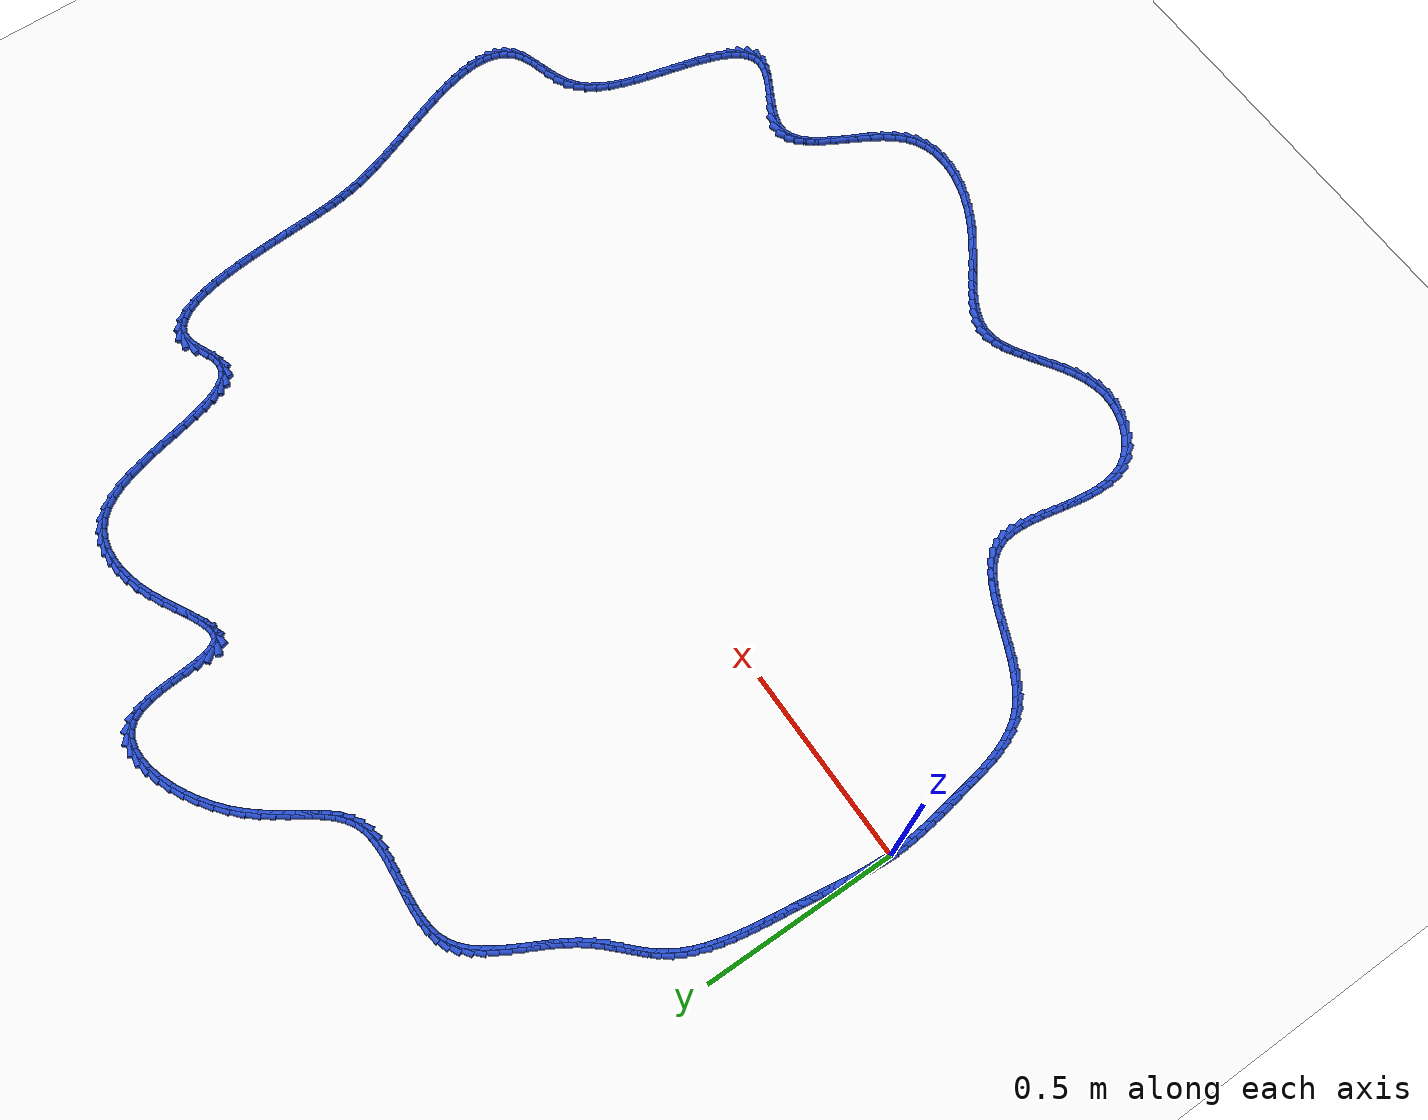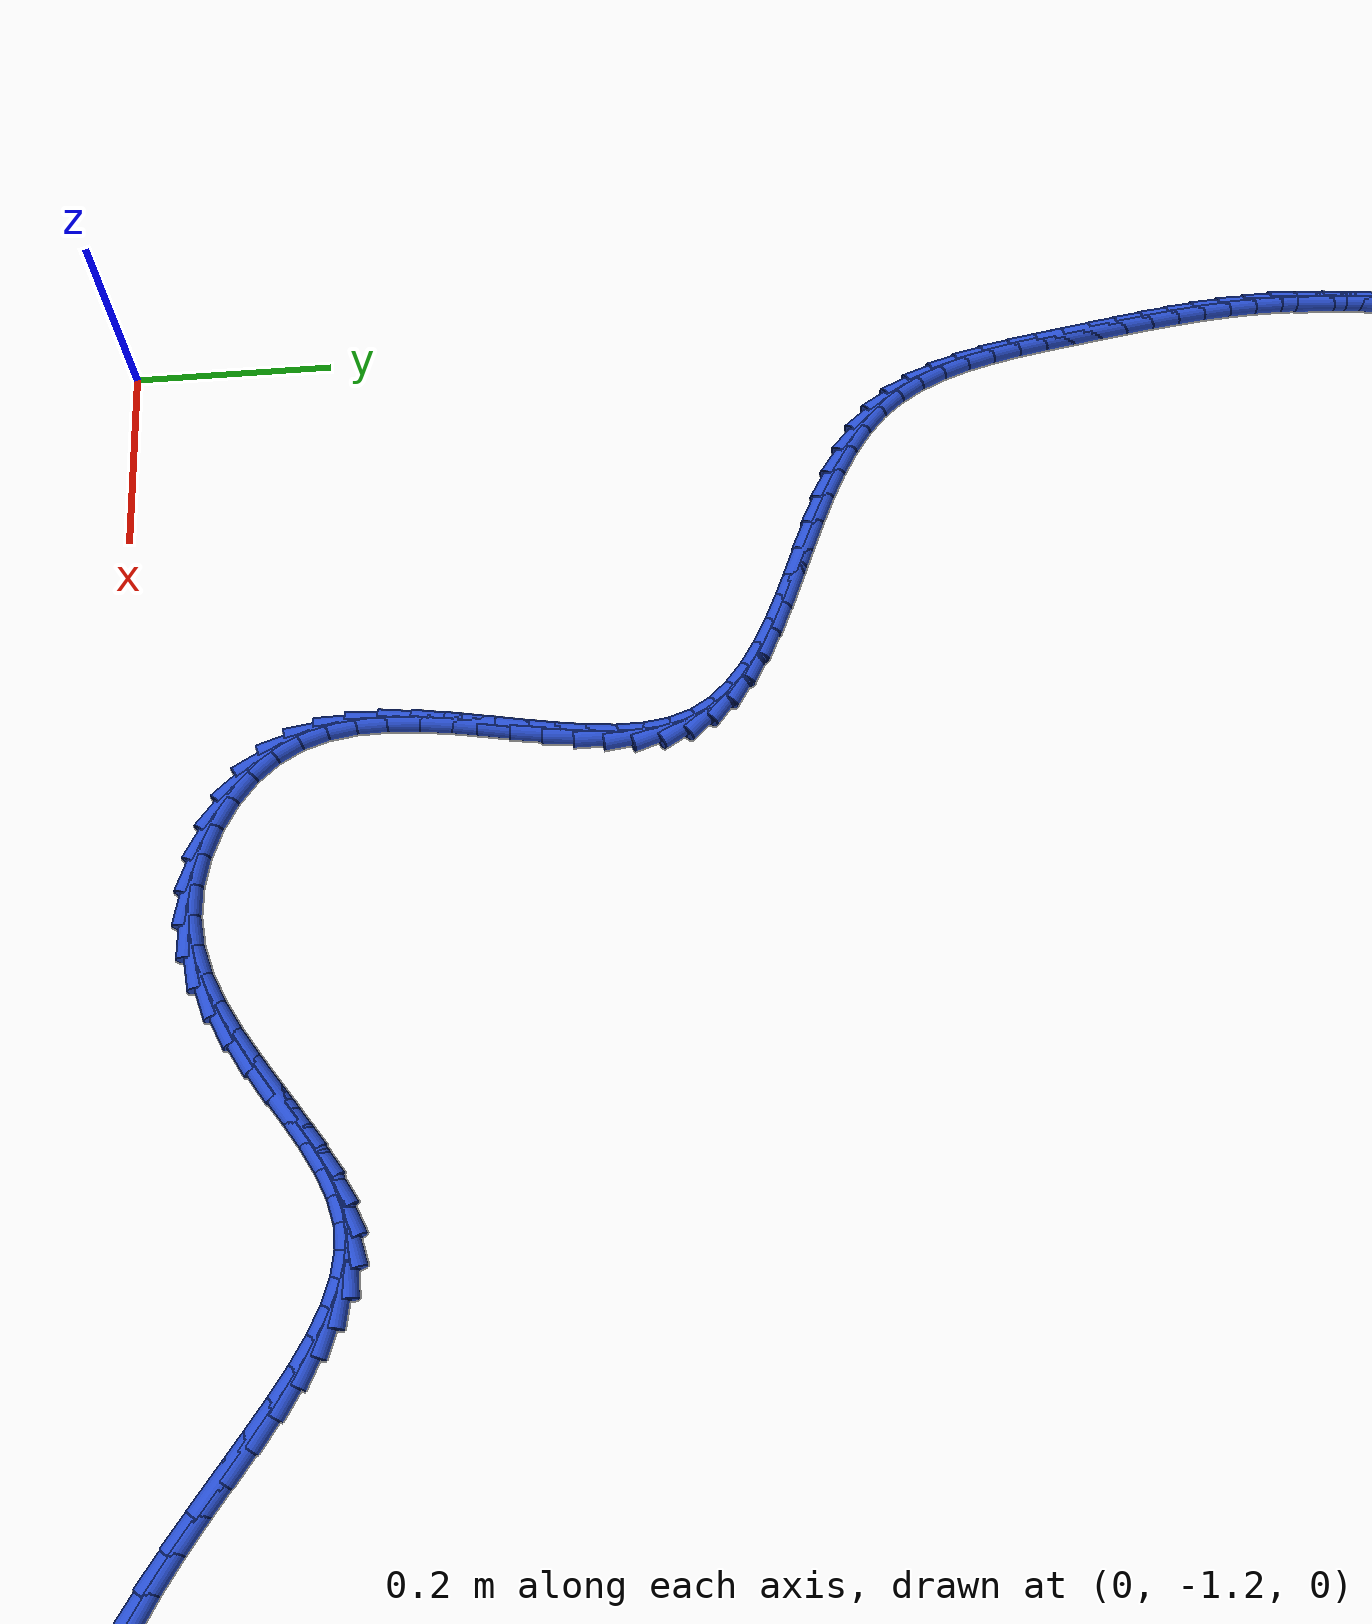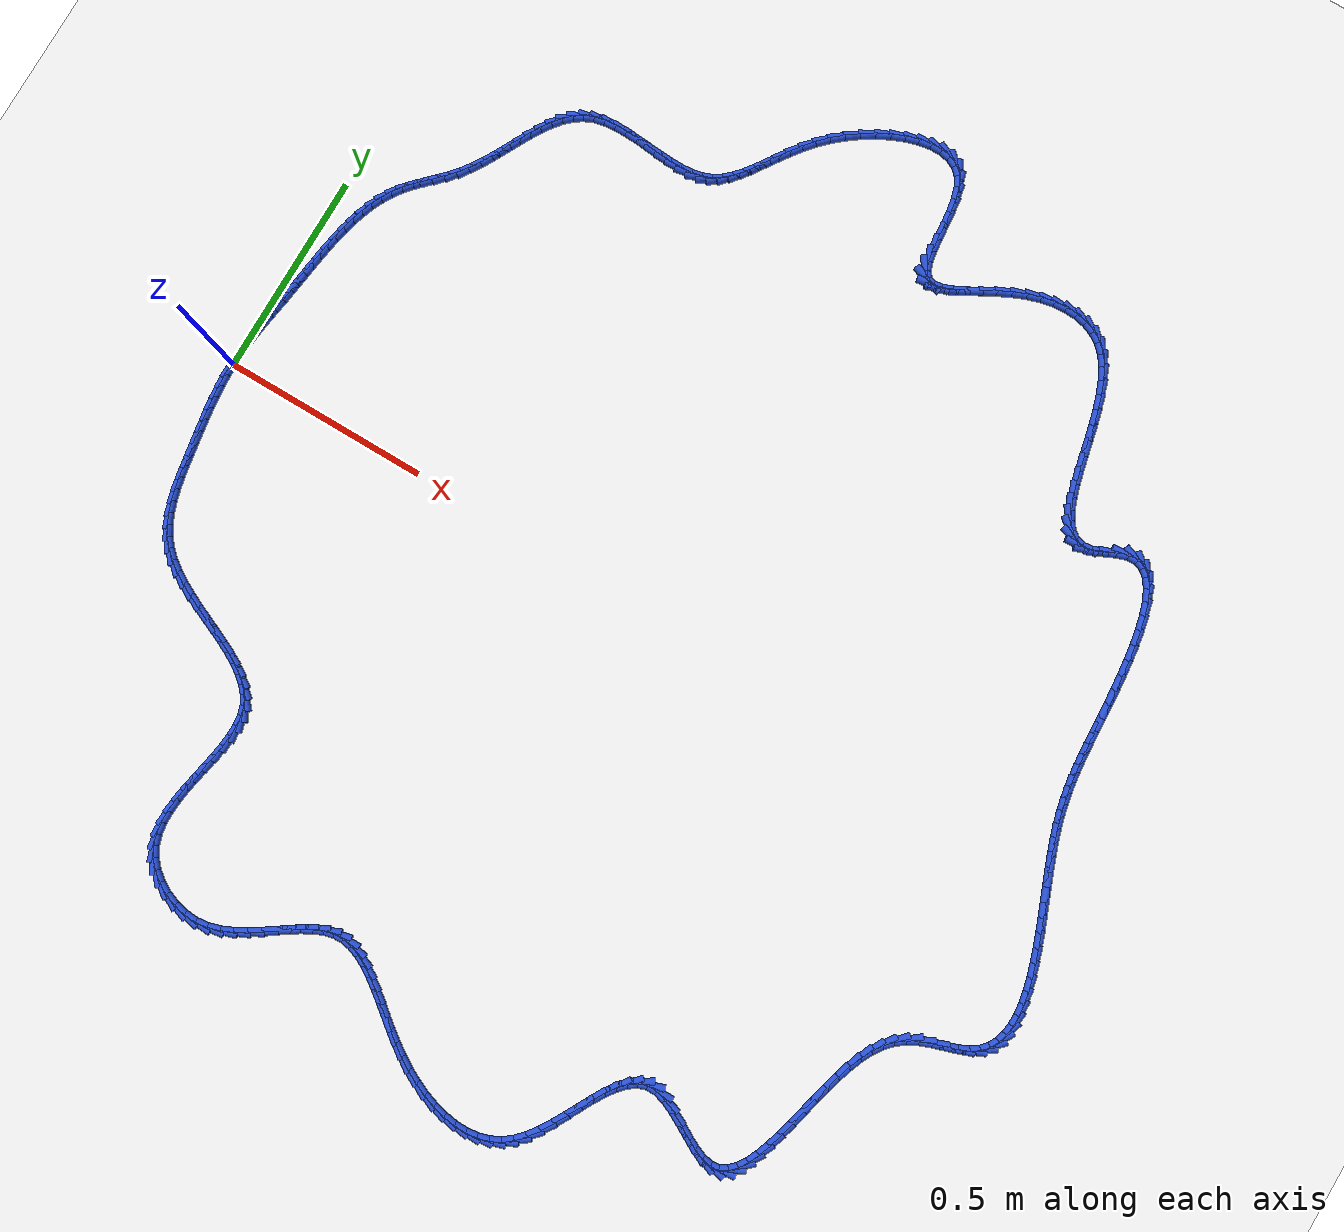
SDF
<sdf version="1.6">
 <world name="default">
  <light name="sun" type="directional">
   <pose>0 0 10 0 -0 0</pose>
   <diffuse>0.8 0.8 0.8 1</diffuse>
   <specular>0.2 0.2 0.2 1</specular>
   <attenuation>
    <range>1000</range>
    <constant>0.9</constant>
    <linear>0.01</linear>
    <quadratic>0.001</quadratic>
   </attenuation>
   <direction>-0.5 0.1 -0.9</direction>
  </light>
  <model name="ground_plane">
   <static>1</static>
   <link name="link">
    <collision name="collision">
     <geometry><plane><normal>0 0 1</normal><size>100 100</size></plane></geometry>
     <surface><friction><ode><mu>100</mu><mu2>50</mu2></ode></friction></surface>
    </collision>
    <visual name="visual">
     <cast_shadows>0</cast_shadows>
     <geometry><plane><normal>0 0 1</normal><size>100 100</size></plane></geometry>
     <material>
      <script><uri>file://media/materials/scripts/gazebo.material</uri><name>Gazebo/WhiteGlow</name></script>
     </material>
    </visual>
   </link>
  </model>
  <gravity>0 0 -9.8</gravity>
  <magnetic_field>6e-06 2.3e-05 -4.2e-05</magnetic_field>
  <atmosphere type="adiabatic"/>
  <physics name="default_physics" default="0" type="ode">
   <max_step_size>0.001</max_step_size>
   <real_time_factor>1</real_time_factor>
   <real_time_update_rate>1000</real_time_update_rate>
  </physics>
  <scene><ambient>0.4 0.4 0.4 1</ambient><background>0.7 0.7 0.7 1</background><shadows>1</shadows></scene>
  <spherical_coordinates>
   <surface_model>EARTH_WGS84</surface_model>
   <latitude_deg>0</latitude_deg>
   <longitude_deg>0</longitude_deg>
   <elevation>0</elevation>
   <heading_deg>0</heading_deg>
  </spherical_coordinates>
  <model name="line">
   <link name="link_0">
    <pose>1.0408340855860843e-17 -6.245004513516506e-17 0.01 0 1.57 1.5413998875680217</pose>
    <collision name="collision">
     <geometry><cylinder><radius>0.01</radius><length>0.08</length></cylinder></geometry>
    </collision>
    <visual name="visual">
     <material>
      <script><name>Gazebo/Blue</name><uri>file://media/materials/scripts/gazebo.material</uri></script>
     </material>
     <geometry><cylinder><radius>0.01</radius><length>0.08</length></cylinder></geometry>
    </visual>
   </link>
   <link name="link_1">
    <pose>0.0008208869173547347 0.027916661631916757 0.01 0 1.57 1.5023600003773971</pose>
    <collision name="collision">
     <geometry><cylinder><radius>0.01</radius><length>0.08</length></cylinder></geometry>
    </collision>
    <visual name="visual">
     <material>
      <script><name>Gazebo/Blue</name><uri>file://media/materials/scripts/gazebo.material</uri></script>
     </material>
     <geometry><cylinder><radius>0.01</radius><length>0.08</length></cylinder></geometry>
    </visual>
   </link>
   <link name="link_2">
    <pose>0.002737069771999113 0.055872434828273414 0.01 0 1.57 1.4710863099867224</pose>
    <collision name="collision">
     <geometry><cylinder><radius>0.01</radius><length>0.08</length></cylinder></geometry>
    </collision>
    <visual name="visual">
     <material>
      <script><name>Gazebo/Blue</name><uri>file://media/materials/scripts/gazebo.material</uri></script>
     </material>
     <geometry><cylinder><radius>0.01</radius><length>0.08</length></cylinder></geometry>
    </visual>
   </link>
   <link name="link_3">
    <pose>0.005542150831564545 0.08391153121294292 0.01 0 1.57 1.447603722277535</pose>
    <collision name="collision">
     <geometry><cylinder><radius>0.01</radius><length>0.08</length></cylinder></geometry>
    </collision>
    <visual name="visual">
     <material>
      <script><name>Gazebo/Blue</name><uri>file://media/materials/scripts/gazebo.material</uri></script>
     </material>
     <geometry><cylinder><radius>0.01</radius><length>0.08</length></cylinder></geometry>
    </visual>
   </link>
   <link name="link_4">
    <pose>0.009029732363682437 0.11207816240979832 0.01 0 1.57 1.4318280480278773</pose>
    <collision name="collision">
     <geometry><cylinder><radius>0.01</radius><length>0.08</length></cylinder></geometry>
    </collision>
    <visual name="visual">
     <material>
      <script><name>Gazebo/Blue</name><uri>file://media/materials/scripts/gazebo.material</uri></script>
     </material>
     <geometry><cylinder><radius>0.01</radius><length>0.08</length></cylinder></geometry>
    </visual>
   </link>
   <link name="link_5">
    <pose>0.012993416635984195 0.1404165400427126 0.01 0 1.57 1.4236111460160457</pose>
    <collision name="collision">
     <geometry><cylinder><radius>0.01</radius><length>0.08</length></cylinder></geometry>
    </collision>
    <visual name="visual">
     <material>
      <script><name>Gazebo/Blue</name><uri>file://media/materials/scripts/gazebo.material</uri></script>
     </material>
     <geometry><cylinder><radius>0.01</radius><length>0.08</length></cylinder></geometry>
    </visual>
   </link>
   <link name="link_6">
    <pose>0.01722680591610122 0.16897087573555886 0.01 0 1.57 1.4227712841737792</pose>
    <collision name="collision">
     <geometry><cylinder><radius>0.01</radius><length>0.08</length></cylinder></geometry>
    </collision>
    <visual name="visual">
     <material>
      <script><name>Gazebo/Blue</name><uri>file://media/materials/scripts/gazebo.material</uri></script>
     </material>
     <geometry><cylinder><radius>0.01</radius><length>0.08</length></cylinder></geometry>
    </visual>
   </link>
   <link name="link_7">
    <pose>0.021523502471664926 0.19778538111221006 0.01 0 1.57 1.4291004208117595</pose>
    <collision name="collision">
     <geometry><cylinder><radius>0.01</radius><length>0.08</length></cylinder></geometry>
    </collision>
    <visual name="visual">
     <material>
      <script><name>Gazebo/Blue</name><uri>file://media/materials/scripts/gazebo.material</uri></script>
     </material>
     <geometry><cylinder><radius>0.01</radius><length>0.08</length></cylinder></geometry>
    </visual>
   </link>
   <link name="link_8">
    <pose>0.02567735066279493 0.22690415439916856 0.01 0 1.57 1.4385400448607677</pose>
    <collision name="collision">
     <geometry><cylinder><radius>0.01</radius><length>0.08</length></cylinder></geometry>
    </collision>
    <visual name="visual">
     <material>
      <script><name>Gazebo/Blue</name><uri>file://media/materials/scripts/gazebo.material</uri></script>
     </material>
     <geometry><cylinder><radius>0.01</radius><length>0.08</length></cylinder></geometry>
    </visual>
   </link>
   <link name="link_9">
    <pose>0.029590687545915446 0.25632047528417756 0.01 0 1.57 1.4412124151300347</pose>
    <collision name="collision">
     <geometry><cylinder><radius>0.01</radius><length>0.08</length></cylinder></geometry>
    </collision>
    <visual name="visual">
     <material>
      <script><name>Gazebo/Blue</name><uri>file://media/materials/scripts/gazebo.material</uri></script>
     </material>
     <geometry><cylinder><radius>0.01</radius><length>0.08</length></cylinder></geometry>
    </visual>
   </link>
   <link name="link_10">
    <pose>0.03344491497119096 0.28589690806564944 0.01 0 1.57 1.435688284381412</pose>
    <collision name="collision">
     <geometry><cylinder><radius>0.01</radius><length>0.08</length></cylinder></geometry>
    </collision>
    <visual name="visual">
     <material>
      <script><name>Gazebo/Blue</name><uri>file://media/materials/scripts/gazebo.material</uri></script>
     </material>
     <geometry><cylinder><radius>0.01</radius><length>0.08</length></cylinder></geometry>
    </visual>
   </link>
   <link name="link_11">
    <pose>0.03746568724147757 0.31547528896481797 0.01 0 1.57 1.4219181251718982</pose>
    <collision name="collision">
     <geometry><cylinder><radius>0.01</radius><length>0.08</length></cylinder></geometry>
    </collision>
    <visual name="visual">
     <material>
      <script><name>Gazebo/Blue</name><uri>file://media/materials/scripts/gazebo.material</uri></script>
     </material>
     <geometry><cylinder><radius>0.01</radius><length>0.08</length></cylinder></geometry>
    </visual>
   </link>
   <link name="link_12">
    <pose>0.04187865865963135 0.34489745420291695 0.01 0 1.57 1.3996527403171772</pose>
    <collision name="collision">
     <geometry><cylinder><radius>0.01</radius><length>0.08</length></cylinder></geometry>
    </collision>
    <visual name="visual">
     <material>
      <script><name>Gazebo/Blue</name><uri>file://media/materials/scripts/gazebo.material</uri></script>
     </material>
     <geometry><cylinder><radius>0.01</radius><length>0.08</length></cylinder></geometry>
    </visual>
   </link>
   <link name="link_13">
    <pose>0.046909483528508406 0.3740052400011805 0.01 0 1.57 1.3684600635219324</pose>
    <collision name="collision">
     <geometry><cylinder><radius>0.01</radius><length>0.08</length></cylinder></geometry>
    </collision>
    <visual name="visual">
     <material>
      <script><name>Gazebo/Blue</name><uri>file://media/materials/scripts/gazebo.material</uri></script>
     </material>
     <geometry><cylinder><radius>0.01</radius><length>0.08</length></cylinder></geometry>
    </visual>
   </link>
   <link name="link_14">
    <pose>0.0527838161509648 0.40264048258084234 0.01 0 1.57 1.3277557386967336</pose>
    <collision name="collision">
     <geometry><cylinder><radius>0.01</radius><length>0.08</length></cylinder></geometry>
    </collision>
    <visual name="visual">
     <material>
      <script><name>Gazebo/Blue</name><uri>file://media/materials/scripts/gazebo.material</uri></script>
     </material>
     <geometry><cylinder><radius>0.01</radius><length>0.08</length></cylinder></geometry>
    </visual>
   </link>
   <link name="link_15">
    <pose>0.05972731082985665 0.4306450181631361 0.01 0 1.57 1.2768599603356972</pose>
    <collision name="collision">
     <geometry><cylinder><radius>0.01</radius><length>0.08</length></cylinder></geometry>
    </collision>
    <visual name="visual">
     <material>
      <script><name>Gazebo/Blue</name><uri>file://media/materials/scripts/gazebo.material</uri></script>
     </material>
     <geometry><cylinder><radius>0.01</radius><length>0.08</length></cylinder></geometry>
    </visual>
   </link>
   <link name="link_16">
    <pose>0.06796562186804003 0.4578606829692961 0.01 0 1.57 1.21509815792084</pose>
    <collision name="collision">
     <geometry><cylinder><radius>0.01</radius><length>0.08</length></cylinder></geometry>
    </collision>
    <visual name="visual">
     <material>
      <script><name>Gazebo/Blue</name><uri>file://media/materials/scripts/gazebo.material</uri></script>
     </material>
     <geometry><cylinder><radius>0.01</radius><length>0.08</length></cylinder></geometry>
    </visual>
   </link>
   <link name="link_17">
    <pose>0.07772440356837104 0.4841293132205559 0.01 0 1.57 1.1419649346995482</pose>
    <collision name="collision">
     <geometry><cylinder><radius>0.01</radius><length>0.08</length></cylinder></geometry>
    </collision>
    <visual name="visual">
     <material>
      <script><name>Gazebo/Blue</name><uri>file://media/materials/scripts/gazebo.material</uri></script>
     </material>
     <geometry><cylinder><radius>0.01</radius><length>0.08</length></cylinder></geometry>
    </visual>
   </link>
   <link name="link_18">
    <pose>0.08922931023370567 0.5092927451381491 0.01 0 1.57 1.05736188813486</pose>
    <collision name="collision">
     <geometry><cylinder><radius>0.01</radius><length>0.08</length></cylinder></geometry>
    </collision>
    <visual name="visual">
     <material>
      <script><name>Gazebo/Blue</name><uri>file://media/materials/scripts/gazebo.material</uri></script>
     </material>
     <geometry><cylinder><radius>0.01</radius><length>0.08</length></cylinder></geometry>
    </visual>
   </link>
   <link name="link_19">
    <pose>0.10270599616690018 0.5331928149433104 0.01 0 1.57 0.9619524386958013</pose>
    <collision name="collision">
     <geometry><cylinder><radius>0.01</radius><length>0.08</length></cylinder></geometry>
    </collision>
    <visual name="visual">
     <material>
      <script><name>Gazebo/Blue</name><uri>file://media/materials/scripts/gazebo.material</uri></script>
     </material>
     <geometry><cylinder><radius>0.01</radius><length>0.08</length></cylinder></geometry>
    </visual>
   </link>
   <link name="link_20">
    <pose>0.11837880055604023 0.5556724736370117 0.01 0 1.57 0.8703472694890867</pose>
    <collision name="collision">
     <geometry><cylinder><radius>0.01</radius><length>0.08</length></cylinder></geometry>
    </collision>
    <visual name="visual">
     <material>
      <script><name>Gazebo/Blue</name><uri>file://media/materials/scripts/gazebo.material</uri></script>
     </material>
     <geometry><cylinder><radius>0.01</radius><length>0.08</length></cylinder></geometry>
    </visual>
   </link>
   <link name="link_21">
    <pose>0.136197057925995 0.5768077846706166 0.01 0 1.57 0.8127109693033912</pose>
    <collision name="collision">
     <geometry><cylinder><radius>0.01</radius><length>0.08</length></cylinder></geometry>
    </collision>
    <visual name="visual">
     <material>
      <script><name>Gazebo/Blue</name><uri>file://media/materials/scripts/gazebo.material</uri></script>
     </material>
     <geometry><cylinder><radius>0.01</radius><length>0.08</length></cylinder></geometry>
    </visual>
   </link>
   <link name="link_22">
    <pose>0.15549838664240928 0.5971933432583749 0.01 0 1.57 0.7918627206875671</pose>
    <collision name="collision">
     <geometry><cylinder><radius>0.01</radius><length>0.08</length></cylinder></geometry>
    </collision>
    <visual name="visual">
     <material>
      <script><name>Gazebo/Blue</name><uri>file://media/materials/scripts/gazebo.material</uri></script>
     </material>
     <geometry><cylinder><radius>0.01</radius><length>0.08</length></cylinder></geometry>
    </visual>
   </link>
   <link name="link_23">
    <pose>0.17553792268249344 0.61749366223505 0.01 0 1.57 0.8060909246171055</pose>
    <collision name="collision">
     <geometry><cylinder><radius>0.01</radius><length>0.08</length></cylinder></geometry>
    </collision>
    <visual name="visual">
     <material>
      <script><name>Gazebo/Blue</name><uri>file://media/materials/scripts/gazebo.material</uri></script>
     </material>
     <geometry><cylinder><radius>0.01</radius><length>0.08</length></cylinder></geometry>
    </visual>
   </link>
   <link name="link_24">
    <pose>0.1955708020234577 0.6383732544354047 0.01 0 1.57 0.8539306330925338</pose>
    <collision name="collision">
     <geometry><cylinder><radius>0.01</radius><length>0.08</length></cylinder></geometry>
    </collision>
    <visual name="visual">
     <material>
      <script><name>Gazebo/Blue</name><uri>file://media/materials/scripts/gazebo.material</uri></script>
     </material>
     <geometry><cylinder><radius>0.01</radius><length>0.08</length></cylinder></geometry>
    </visual>
   </link>
   <link name="link_25">
    <pose>0.2148521606425124 0.6604966326942023 0.01 0 1.57 0.9313257227222355</pose>
    <collision name="collision">
     <geometry><cylinder><radius>0.01</radius><length>0.08</length></cylinder></geometry>
    </collision>
    <visual name="visual">
     <material>
      <script><name>Gazebo/Blue</name><uri>file://media/materials/scripts/gazebo.material</uri></script>
     </material>
     <geometry><cylinder><radius>0.01</radius><length>0.08</length></cylinder></geometry>
    </visual>
   </link>
   <link name="link_26">
    <pose>0.23268545992700843 0.6844751038121927 0.01 0 1.57 1.0055148349731493</pose>
    <collision name="collision">
     <geometry><cylinder><radius>0.01</radius><length>0.08</length></cylinder></geometry>
    </collision>
    <visual name="visual">
     <material>
      <script><name>Gazebo/Blue</name><uri>file://media/materials/scripts/gazebo.material</uri></script>
     </material>
     <geometry><cylinder><radius>0.01</radius><length>0.08</length></cylinder></geometry>
    </visual>
   </link>
   <link name="link_27">
    <pose>0.24901365503186382 0.7102158951617413 0.01 0 1.57 1.0561269612380986</pose>
    <collision name="collision">
     <geometry><cylinder><radius>0.01</radius><length>0.08</length></cylinder></geometry>
    </collision>
    <visual name="visual">
     <material>
      <script><name>Gazebo/Blue</name><uri>file://media/materials/scripts/gazebo.material</uri></script>
     </material>
     <geometry><cylinder><radius>0.01</radius><length>0.08</length></cylinder></geometry>
    </visual>
   </link>
   <link name="link_28">
    <pose>0.2642324517653138 0.7371277579183291 0.01 0 1.57 1.0848685483043983</pose>
    <collision name="collision">
     <geometry><cylinder><radius>0.01</radius><length>0.08</length></cylinder></geometry>
    </collision>
    <visual name="visual">
     <material>
      <script><name>Gazebo/Blue</name><uri>file://media/materials/scripts/gazebo.material</uri></script>
     </material>
     <geometry><cylinder><radius>0.01</radius><length>0.08</length></cylinder></geometry>
    </visual>
   </link>
   <link name="link_29">
    <pose>0.2787471308507492 0.7646089013239075 0.01 0 1.57 1.0929258770759624</pose>
    <collision name="collision">
     <geometry><cylinder><radius>0.01</radius><length>0.08</length></cylinder></geometry>
    </collision>
    <visual name="visual">
     <material>
      <script><name>Gazebo/Blue</name><uri>file://media/materials/scripts/gazebo.material</uri></script>
     </material>
     <geometry><cylinder><radius>0.01</radius><length>0.08</length></cylinder></geometry>
    </visual>
   </link>
   <link name="link_30">
    <pose>0.29296297301156105 0.7920575346204286 0.01 0 1.57 1.0802205135491318</pose>
    <collision name="collision">
     <geometry><cylinder><radius>0.01</radius><length>0.08</length></cylinder></geometry>
    </collision>
    <visual name="visual">
     <material>
      <script><name>Gazebo/Blue</name><uri>file://media/materials/scripts/gazebo.material</uri></script>
     </material>
     <geometry><cylinder><radius>0.01</radius><length>0.08</length></cylinder></geometry>
    </visual>
   </link>
   <link name="link_31">
    <pose>0.30728525897114034 0.8188718670498436 0.01 0 1.57 1.045252589005371</pose>
    <collision name="collision">
     <geometry><cylinder><radius>0.01</radius><length>0.08</length></cylinder></geometry>
    </collision>
    <visual name="visual">
     <material>
      <script><name>Gazebo/Blue</name><uri>file://media/materials/scripts/gazebo.material</uri></script>
     </material>
     <geometry><cylinder><radius>0.01</radius><length>0.08</length></cylinder></geometry>
    </visual>
   </link>
   <link name="link_32">
    <pose>0.3221192694528783 0.8444501078541052 0.01 0 1.57 0.9850100628299966</pose>
    <collision name="collision">
     <geometry><cylinder><radius>0.01</radius><length>0.08</length></cylinder></geometry>
    </collision>
    <visual name="visual">
     <material>
      <script><name>Gazebo/Blue</name><uri>file://media/materials/scripts/gazebo.material</uri></script>
     </material>
     <geometry><cylinder><radius>0.01</radius><length>0.08</length></cylinder></geometry>
    </visual>
   </link>
   <link name="link_33">
    <pose>0.33787028518016565 0.8681904662751646 0.01 0 1.57 0.8951184825784314</pose>
    <collision name="collision">
     <geometry><cylinder><radius>0.01</radius><length>0.08</length></cylinder></geometry>
    </collision>
    <visual name="visual">
     <material>
      <script><name>Gazebo/Blue</name><uri>file://media/materials/scripts/gazebo.material</uri></script>
     </material>
     <geometry><cylinder><radius>0.01</radius><length>0.08</length></cylinder></geometry>
    </visual>
   </link>
   <link name="link_34">
    <pose>0.3549435868763936 0.889491151554974 0.01 0 1.57 0.7707838316606739</pose>
    <collision name="collision">
     <geometry><cylinder><radius>0.01</radius><length>0.08</length></cylinder></geometry>
    </collision>
    <visual name="visual">
     <material>
      <script><name>Gazebo/Blue</name><uri>file://media/materials/scripts/gazebo.material</uri></script>
     </material>
     <geometry><cylinder><radius>0.01</radius><length>0.08</length></cylinder></geometry>
    </visual>
   </link>
   <link name="link_35">
    <pose>0.3737444552649532 0.9077503729354849 0.01 0 1.57 0.6095183773093915</pose>
    <collision name="collision">
     <geometry><cylinder><radius>0.01</radius><length>0.08</length></cylinder></geometry>
    </collision>
    <visual name="visual">
     <material>
      <script><name>Gazebo/Blue</name><uri>file://media/materials/scripts/gazebo.material</uri></script>
     </material>
     <geometry><cylinder><radius>0.01</radius><length>0.08</length></cylinder></geometry>
    </visual>
   </link>
   <link name="link_36">
    <pose>0.3946781710692351 0.922366339658649 0.01 0 1.57 0.4169142393225173</pose>
    <collision name="collision">
     <geometry><cylinder><radius>0.01</radius><length>0.08</length></cylinder></geometry>
    </collision>
    <visual name="visual">
     <material>
      <script><name>Gazebo/Blue</name><uri>file://media/materials/scripts/gazebo.material</uri></script>
     </material>
     <geometry><cylinder><radius>0.01</radius><length>0.08</length></cylinder></geometry>
    </visual>
   </link>
   <link name="link_37">
    <pose>0.418137802423669 0.9327560586852598 0.01 0 1.57 0.2342398182294077</pose>
    <collision name="collision">
     <geometry><cylinder><radius>0.01</radius><length>0.08</length></cylinder></geometry>
    </collision>
    <visual name="visual">
     <material>
      <script><name>Gazebo/Blue</name><uri>file://media/materials/scripts/gazebo.material</uri></script>
     </material>
     <geometry><cylinder><radius>0.01</radius><length>0.08</length></cylinder></geometry>
    </visual>
   </link>
   <link name="link_38">
    <pose>0.4441148099556708 0.938954694602212 0.01 0 1.57 0.099165189854547</pose>
    <collision name="collision">
     <geometry><cylinder><radius>0.01</radius><length>0.08</length></cylinder></geometry>
    </collision>
    <visual name="visual">
     <material>
      <script><name>Gazebo/Blue</name><uri>file://media/materials/scripts/gazebo.material</uri></script>
     </material>
     <geometry><cylinder><radius>0.01</radius><length>0.08</length></cylinder></geometry>
    </visual>
   </link>
   <link name="link_39">
    <pose>0.4721177209583363 0.9417407470145399 0.01 0 1.57 0.0066443476232158055</pose>
    <collision name="collision">
     <geometry><cylinder><radius>0.01</radius><length>0.08</length></cylinder></geometry>
    </collision>
    <visual name="visual">
     <material>
      <script><name>Gazebo/Blue</name><uri>file://media/materials/scripts/gazebo.material</uri></script>
     </material>
     <geometry><cylinder><radius>0.01</radius><length>0.08</length></cylinder></geometry>
    </visual>
   </link>
   <link name="link_40">
    <pose>0.5016264113924837 0.9419368158970063 0.01 0 1.57 -0.051482534014663094</pose>
    <collision name="collision">
     <geometry><cylinder><radius>0.01</radius><length>0.08</length></cylinder></geometry>
    </collision>
    <visual name="visual">
     <material>
      <script><name>Gazebo/Blue</name><uri>file://media/materials/scripts/gazebo.material</uri></script>
     </material>
     <geometry><cylinder><radius>0.01</radius><length>0.08</length></cylinder></geometry>
    </visual>
   </link>
   <link name="link_41">
    <pose>0.5321207572189316 0.9403655012243733 0.01 0 1.57 -0.08109142949023493</pose>
    <collision name="collision">
     <geometry><cylinder><radius>0.01</radius><length>0.08</length></cylinder></geometry>
    </collision>
    <visual name="visual">
     <material>
      <script><name>Gazebo/Blue</name><uri>file://media/materials/scripts/gazebo.material</uri></script>
     </material>
     <geometry><cylinder><radius>0.01</radius><length>0.08</length></cylinder></geometry>
    </visual>
   </link>
   <link name="link_42">
    <pose>0.5630806343984984 0.9378494029714038 0.01 0 1.57 -0.08516022348309951</pose>
    <collision name="collision">
     <geometry><cylinder><radius>0.01</radius><length>0.08</length></cylinder></geometry>
    </collision>
    <visual name="visual">
     <material>
      <script><name>Gazebo/Blue</name><uri>file://media/materials/scripts/gazebo.material</uri></script>
     </material>
     <geometry><cylinder><radius>0.01</radius><length>0.08</length></cylinder></geometry>
    </visual>
   </link>
   <link name="link_43">
    <pose>0.5939859188920031 0.93521112111286 0.01 0 1.57 -0.06380477526195301</pose>
    <collision name="collision">
     <geometry><cylinder><radius>0.01</radius><length>0.08</length></cylinder></geometry>
    </collision>
    <visual name="visual">
     <material>
      <script><name>Gazebo/Blue</name><uri>file://media/materials/scripts/gazebo.material</uri></script>
     </material>
     <geometry><cylinder><radius>0.01</radius><length>0.08</length></cylinder></geometry>
    </visual>
   </link>
   <link name="link_44">
    <pose>0.6243164866602637 0.9332732556235039 0.01 0 1.57 -0.014188848642629209</pose>
    <collision name="collision">
     <geometry><cylinder><radius>0.01</radius><length>0.08</length></cylinder></geometry>
    </collision>
    <visual name="visual">
     <material>
      <script><name>Gazebo/Blue</name><uri>file://media/materials/scripts/gazebo.material</uri></script>
     </material>
     <geometry><cylinder><radius>0.01</radius><length>0.08</length></cylinder></geometry>
    </visual>
   </link>
   <link name="link_45">
    <pose>0.6535522136640988 0.9328584064780986 0.01 0 1.57 0.06978922296196566</pose>
    <collision name="collision">
     <geometry><cylinder><radius>0.01</radius><length>0.08</length></cylinder></geometry>
    </collision>
    <visual name="visual">
     <material>
      <script><name>Gazebo/Blue</name><uri>file://media/materials/scripts/gazebo.material</uri></script>
     </material>
     <geometry><cylinder><radius>0.01</radius><length>0.08</length></cylinder></geometry>
    </visual>
   </link>
   <link name="link_46">
    <pose>0.6811729758643272 0.9347891736514062 0.01 0 1.57 0.19746531131207593</pose>
    <collision name="collision">
     <geometry><cylinder><radius>0.01</radius><length>0.08</length></cylinder></geometry>
    </collision>
    <visual name="visual">
     <material>
      <script><name>Gazebo/Blue</name><uri>file://media/materials/scripts/gazebo.material</uri></script>
     </material>
     <geometry><cylinder><radius>0.01</radius><length>0.08</length></cylinder></geometry>
    </visual>
   </link>
   <link name="link_47">
    <pose>0.706658649221767 0.9398881571181894 0.01 0 1.57 0.37600592923872767</pose>
    <collision name="collision">
     <geometry><cylinder><radius>0.01</radius><length>0.08</length></cylinder></geometry>
    </collision>
    <visual name="visual">
     <material>
      <script><name>Gazebo/Blue</name><uri>file://media/materials/scripts/gazebo.material</uri></script>
     </material>
     <geometry><cylinder><radius>0.01</radius><length>0.08</length></cylinder></geometry>
    </visual>
   </link>
   <link name="link_48">
    <pose>0.7295363438716603 0.9489200153381636 0.01 0 1.57 0.5663426184428318</pose>
    <collision name="collision">
     <geometry><cylinder><radius>0.01</radius><length>0.08</length></cylinder></geometry>
    </collision>
    <visual name="visual">
     <material>
      <script><name>Gazebo/Blue</name><uri>file://media/materials/scripts/gazebo.material</uri></script>
     </material>
     <geometry><cylinder><radius>0.01</radius><length>0.08</length></cylinder></geometry>
    </visual>
   </link>
   <link name="link_49">
    <pose>0.7499464086456047 0.9618971552585215 0.01 0 1.57 0.7252811947216745</pose>
    <collision name="collision">
     <geometry><cylinder><radius>0.01</radius><length>0.08</length></cylinder></geometry>
    </collision>
    <visual name="visual">
     <material>
      <script><name>Gazebo/Blue</name><uri>file://media/materials/scripts/gazebo.material</uri></script>
     </material>
     <geometry><cylinder><radius>0.01</radius><length>0.08</length></cylinder></geometry>
    </visual>
   </link>
   <link name="link_50">
    <pose>0.7684575833105038 0.9783064825315326 0.01 0 1.57 0.8436183278955764</pose>
    <collision name="collision">
     <geometry><cylinder><radius>0.01</radius><length>0.08</length></cylinder></geometry>
    </collision>
    <visual name="visual">
     <material>
      <script><name>Gazebo/Blue</name><uri>file://media/materials/scripts/gazebo.material</uri></script>
     </material>
     <geometry><cylinder><radius>0.01</radius><length>0.08</length></cylinder></geometry>
    </visual>
   </link>
   <link name="link_51">
    <pose>0.7856473744890136 0.9976241486275458 0.01 0 1.57 0.9223212880032153</pose>
    <collision name="collision">
     <geometry><cylinder><radius>0.01</radius><length>0.08</length></cylinder></geometry>
    </collision>
    <visual name="visual">
     <material>
      <script><name>Gazebo/Blue</name><uri>file://media/materials/scripts/gazebo.material</uri></script>
     </material>
     <geometry><cylinder><radius>0.01</radius><length>0.08</length></cylinder></geometry>
    </visual>
   </link>
   <link name="link_52">
    <pose>0.8020932888037904 1.0193263050169106 0.01 0 1.57 0.9662036940306503</pose>
    <collision name="collision">
     <geometry><cylinder><radius>0.01</radius><length>0.08</length></cylinder></geometry>
    </collision>
    <visual name="visual">
     <material>
      <script><name>Gazebo/Blue</name><uri>file://media/materials/scripts/gazebo.material</uri></script>
     </material>
     <geometry><cylinder><radius>0.01</radius><length>0.08</length></cylinder></geometry>
    </visual>
   </link>
   <link name="link_53">
    <pose>0.8183728328774906 1.0428891031699763 0.01 0 1.57 0.9802691333980146</pose>
    <collision name="collision">
     <geometry><cylinder><radius>0.01</radius><length>0.08</length></cylinder></geometry>
    </collision>
    <visual name="visual">
     <material>
      <script><name>Gazebo/Blue</name><uri>file://media/materials/scripts/gazebo.material</uri></script>
     </material>
     <geometry><cylinder><radius>0.01</radius><length>0.08</length></cylinder></geometry>
    </visual>
   </link>
   <link name="link_54">
    <pose>0.8350635133327708 1.0677886945570925 0.01 0 1.57 0.9684573554207071</pose>
    <collision name="collision">
     <geometry><cylinder><radius>0.01</radius><length>0.08</length></cylinder></geometry>
    </collision>
    <visual name="visual">
     <material>
      <script><name>Gazebo/Blue</name><uri>file://media/materials/scripts/gazebo.material</uri></script>
     </material>
     <geometry><cylinder><radius>0.01</radius><length>0.08</length></cylinder></geometry>
    </visual>
   </link>
   <link name="link_55">
    <pose>0.8527428367922871 1.093501230648608 0.01 0 1.57 0.9336200118960726</pose>
    <collision name="collision">
     <geometry><cylinder><radius>0.01</radius><length>0.08</length></cylinder></geometry>
    </collision>
    <visual name="visual">
     <material>
      <script><name>Gazebo/Blue</name><uri>file://media/materials/scripts/gazebo.material</uri></script>
     </material>
     <geometry><cylinder><radius>0.01</radius><length>0.08</length></cylinder></geometry>
    </visual>
   </link>
   <link name="link_56">
    <pose>0.871988309878696 1.1195028629148727 0.01 0 1.57 0.8779683117536206</pose>
    <collision name="collision">
     <geometry><cylinder><radius>0.01</radius><length>0.08</length></cylinder></geometry>
    </collision>
    <visual name="visual">
     <material>
      <script><name>Gazebo/Blue</name><uri>file://media/materials/scripts/gazebo.material</uri></script>
     </material>
     <geometry><cylinder><radius>0.01</radius><length>0.08</length></cylinder></geometry>
    </visual>
   </link>
   <link name="link_57">
    <pose>0.8933774392146541 1.1452697428262357 0.01 0 1.57 0.8036944621611402</pose>
    <collision name="collision">
     <geometry><cylinder><radius>0.01</radius><length>0.08</length></cylinder></geometry>
    </collision>
    <visual name="visual">
     <material>
      <script><name>Gazebo/Blue</name><uri>file://media/materials/scripts/gazebo.material</uri></script>
     </material>
     <geometry><cylinder><radius>0.01</radius><length>0.08</length></cylinder></geometry>
    </visual>
   </link>
   <link name="link_58">
    <pose>0.917486950826704 1.1702780286261705 0.01 0 1.57 0.7196453990966106</pose>
    <collision name="collision">
     <geometry><cylinder><radius>0.01</radius><length>0.08</length></cylinder></geometry>
    </collision>
    <visual name="visual">
     <material>
      <script><name>Gazebo/Blue</name><uri>file://media/materials/scripts/gazebo.material</uri></script>
     </material>
     <geometry><cylinder><radius>0.01</radius><length>0.08</length></cylinder></geometry>
    </visual>
   </link>
   <link name="link_59">
    <pose>0.9445609282666728 1.1940067648509556 0.01 0 1.57 0.640452583252448</pose>
    <collision name="collision">
     <geometry><cylinder><radius>0.01</radius><length>0.08</length></cylinder></geometry>
    </collision>
    <visual name="visual">
     <material>
      <script><name>Gazebo/Blue</name><uri>file://media/materials/scripts/gazebo.material</uri></script>
     </material>
     <geometry><cylinder><radius>0.01</radius><length>0.08</length></cylinder></geometry>
    </visual>
   </link>
   <link name="link_60">
    <pose>0.9739948989982113 1.2159423588408294 0.01 0 1.57 0.563675499750834</pose>
    <collision name="collision">
     <geometry><cylinder><radius>0.01</radius><length>0.08</length></cylinder></geometry>
    </collision>
    <visual name="visual">
     <material>
      <script><name>Gazebo/Blue</name><uri>file://media/materials/scripts/gazebo.material</uri></script>
     </material>
     <geometry><cylinder><radius>0.01</radius><length>0.08</length></cylinder></geometry>
    </visual>
   </link>
   <link name="link_61">
    <pose>1.0050510414973604 1.2355723749867777 0.01 0 1.57 0.4845077665282798</pose>
    <collision name="collision">
     <geometry><cylinder><radius>0.01</radius><length>0.08</length></cylinder></geometry>
    </collision>
    <visual name="visual">
     <material>
      <script><name>Gazebo/Blue</name><uri>file://media/materials/scripts/gazebo.material</uri></script>
     </material>
     <geometry><cylinder><radius>0.01</radius><length>0.08</length></cylinder></geometry>
    </visual>
   </link>
   <link name="link_62">
    <pose>1.0369915342401606 1.2523843776797845 0.01 0 1.57 0.397760566701612</pose>
    <collision name="collision">
     <geometry><cylinder><radius>0.01</radius><length>0.08</length></cylinder></geometry>
    </collision>
    <visual name="visual">
     <material>
      <script><name>Gazebo/Blue</name><uri>file://media/materials/scripts/gazebo.material</uri></script>
     </material>
     <geometry><cylinder><radius>0.01</radius><length>0.08</length></cylinder></geometry>
    </visual>
   </link>
   <link name="link_63">
    <pose>1.0690785557026525 1.2658659313108347 0.01 0 1.57 0.29698058577774566</pose>
    <collision name="collision">
     <geometry><cylinder><radius>0.01</radius><length>0.08</length></cylinder></geometry>
    </collision>
    <visual name="visual">
     <material>
      <script><name>Gazebo/Blue</name><uri>file://media/materials/scripts/gazebo.material</uri></script>
     </material>
     <geometry><cylinder><radius>0.01</radius><length>0.08</length></cylinder></geometry>
    </visual>
   </link>
   <link name="link_64">
    <pose>1.1005742843608772 1.2755046002709138 0.01 0 1.57 0.1733804689775308</pose>
    <collision name="collision">
     <geometry><cylinder><radius>0.01</radius><length>0.08</length></cylinder></geometry>
    </collision>
    <visual name="visual">
     <material>
      <script><name>Gazebo/Blue</name><uri>file://media/materials/scripts/gazebo.material</uri></script>
     </material>
     <geometry><cylinder><radius>0.01</radius><length>0.08</length></cylinder></geometry>
    </visual>
   </link>
   <link name="link_65">
    <pose>1.1307408986908751 1.2807879489510063 0.01 0 1.57 0.014788870014408064</pose>
    <collision name="collision">
     <geometry><cylinder><radius>0.01</radius><length>0.08</length></cylinder></geometry>
    </collision>
    <visual name="visual">
     <material>
      <script><name>Gazebo/Blue</name><uri>file://media/materials/scripts/gazebo.material</uri></script>
     </material>
     <geometry><cylinder><radius>0.01</radius><length>0.08</length></cylinder></geometry>
    </visual>
   </link>
   <link name="link_66">
    <pose>1.1588405771686872 1.2812035417420966 0.01 0 1.57 -0.19380511252535743</pose>
    <collision name="collision">
     <geometry><cylinder><radius>0.01</radius><length>0.08</length></cylinder></geometry>
    </collision>
    <visual name="visual">
     <material>
      <script><name>Gazebo/Blue</name><uri>file://media/materials/scripts/gazebo.material</uri></script>
     </material>
     <geometry><cylinder><radius>0.01</radius><length>0.08</length></cylinder></geometry>
    </visual>
   </link>
   <link name="link_67">
    <pose>1.184135498270354 1.2762389430351704 0.01 0 1.57 -0.4629506031863374</pose>
    <collision name="collision">
     <geometry><cylinder><radius>0.01</radius><length>0.08</length></cylinder></geometry>
    </collision>
    <visual name="visual">
     <material>
      <script><name>Gazebo/Blue</name><uri>file://media/materials/scripts/gazebo.material</uri></script>
     </material>
     <geometry><cylinder><radius>0.01</radius><length>0.08</length></cylinder></geometry>
    </visual>
   </link>
   <link name="link_68">
    <pose>1.2058878404719158 1.265381717221211 0.01 0 1.57 -0.7793623105907405</pose>
    <collision name="collision">
     <geometry><cylinder><radius>0.01</radius><length>0.08</length></cylinder></geometry>
    </collision>
    <visual name="visual">
     <material>
      <script><name>Gazebo/Blue</name><uri>file://media/materials/scripts/gazebo.material</uri></script>
     </material>
     <geometry><cylinder><radius>0.01</radius><length>0.08</length></cylinder></geometry>
    </visual>
   </link>
   <link name="link_69">
    <pose>1.223359782249414 1.2481194286912047 0.01 0 1.57 -1.0833287653201922</pose>
    <collision name="collision">
     <geometry><cylinder><radius>0.01</radius><length>0.08</length></cylinder></geometry>
    </collision>
    <visual name="visual">
     <material>
      <script><name>Gazebo/Blue</name><uri>file://media/materials/scripts/gazebo.material</uri></script>
     </material>
     <geometry><cylinder><radius>0.01</radius><length>0.08</length></cylinder></geometry>
    </visual>
   </link>
   <link name="link_70">
    <pose>1.2360315128929988 1.2242167989494697 0.01 0 1.57 -1.2853422062372333</pose>
    <collision name="collision">
     <geometry><cylinder><radius>0.01</radius><length>0.08</length></cylinder></geometry>
    </collision>
    <visual name="visual">
     <material>
      <script><name>Gazebo/Blue</name><uri>file://media/materials/scripts/gazebo.material</uri></script>
     </material>
     <geometry><cylinder><radius>0.01</radius><length>0.08</length></cylinder></geometry>
    </visual>
   </link>
   <link name="link_71">
    <pose>1.244607285723089 1.194994701907489 0.01 0 1.57 -1.4007492171855416</pose>
    <collision name="collision">
     <geometry><cylinder><radius>0.01</radius><length>0.08</length></cylinder></geometry>
    </collision>
    <visual name="visual">
     <material>
      <script><name>Gazebo/Blue</name><uri>file://media/materials/scripts/gazebo.material</uri></script>
     </material>
     <geometry><cylinder><radius>0.01</radius><length>0.08</length></cylinder></geometry>
    </visual>
   </link>
   <link name="link_72">
    <pose>1.2502182650615765 1.162316743365079 0.01 0 1.57 -1.4610024508072048</pose>
    <collision name="collision">
     <geometry><cylinder><radius>0.01</radius><length>0.08</length></cylinder></geometry>
    </collision>
    <visual name="visual">
     <material>
      <script><name>Gazebo/Blue</name><uri>file://media/materials/scripts/gazebo.material</uri></script>
     </material>
     <geometry><cylinder><radius>0.01</radius><length>0.08</length></cylinder></geometry>
    </visual>
   </link>
   <link name="link_73">
    <pose>1.2539960555104162 1.1280470888500291 0.01 0 1.57 -1.480557919991473</pose>
    <collision name="collision">
     <geometry><cylinder><radius>0.01</radius><length>0.08</length></cylinder></geometry>
    </collision>
    <visual name="visual">
     <material>
      <script><name>Gazebo/Blue</name><uri>file://media/materials/scripts/gazebo.material</uri></script>
     </material>
     <geometry><cylinder><radius>0.01</radius><length>0.08</length></cylinder></geometry>
    </visual>
   </link>
   <link name="link_74">
    <pose>1.2570722616715635 1.0940499038901312 0.01 0 1.57 -1.4611882365544484</pose>
    <collision name="collision">
     <geometry><cylinder><radius>0.01</radius><length>0.08</length></cylinder></geometry>
    </collision>
    <visual name="visual">
     <material>
      <script><name>Gazebo/Blue</name><uri>file://media/materials/scripts/gazebo.material</uri></script>
     </material>
     <geometry><cylinder><radius>0.01</radius><length>0.08</length></cylinder></geometry>
    </visual>
   </link>
   <link name="link_75">
    <pose>1.260578488146973 1.0621893540131744 0.01 0 1.57 -1.3908579647973993</pose>
    <collision name="collision">
     <geometry><cylinder><radius>0.01</radius><length>0.08</length></cylinder></geometry>
    </collision>
    <visual name="visual">
     <material>
      <script><name>Gazebo/Blue</name><uri>file://media/materials/scripts/gazebo.material</uri></script>
     </material>
     <geometry><cylinder><radius>0.01</radius><length>0.08</length></cylinder></geometry>
    </visual>
   </link>
   <link name="link_76">
    <pose>1.2656463395386 1.0343296047469495 0.01 0 1.57 -1.2315758286325444</pose>
    <collision name="collision">
     <geometry><cylinder><radius>0.01</radius><length>0.08</length></cylinder></geometry>
    </collision>
    <visual name="visual">
     <material>
      <script><name>Gazebo/Blue</name><uri>file://media/materials/scripts/gazebo.material</uri></script>
     </material>
     <geometry><cylinder><radius>0.01</radius><length>0.08</length></cylinder></geometry>
    </visual>
   </link>
   <link name="link_77">
    <pose>1.2734074204483994 1.0123348216192463 0.01 0 1.57 -0.8886878355725425</pose>
    <collision name="collision">
     <geometry><cylinder><radius>0.01</radius><length>0.08</length></cylinder></geometry>
    </collision>
    <visual name="visual">
     <material>
      <script><name>Gazebo/Blue</name><uri>file://media/materials/scripts/gazebo.material</uri></script>
     </material>
     <geometry><cylinder><radius>0.01</radius><length>0.08</length></cylinder></geometry>
    </visual>
   </link>
   <link name="link_78">
    <pose>1.2849933354783265 0.9980691701578549 0.01 0 1.57 -0.30560761072414755</pose>
    <collision name="collision">
     <geometry><cylinder><radius>0.01</radius><length>0.08</length></cylinder></geometry>
    </collision>
    <visual name="visual">
     <material>
      <script><name>Gazebo/Blue</name><uri>file://media/materials/scripts/gazebo.material</uri></script>
     </material>
     <geometry><cylinder><radius>0.01</radius><length>0.08</length></cylinder></geometry>
    </visual>
   </link>
   <link name="link_79">
    <pose>1.3013005140783682 0.9929243990145776 0.01 0 1.57 0.14129225557697167</pose>
    <collision name="collision">
     <geometry><cylinder><radius>0.01</radius><length>0.08</length></cylinder></geometry>
    </collision>
    <visual name="visual">
     <material>
      <script><name>Gazebo/Blue</name><uri>file://media/materials/scripts/gazebo.material</uri></script>
     </material>
     <geometry><cylinder><radius>0.01</radius><length>0.08</length></cylinder></geometry>
    </visual>
   </link>
   <link name="link_80">
    <pose>1.3220203463864535 0.9958715890857948 0.01 0 1.57 0.36136505471235036</pose>
    <collision name="collision">
     <geometry><cylinder><radius>0.01</radius><length>0.08</length></cylinder></geometry>
    </collision>
    <visual name="visual">
     <material>
      <script><name>Gazebo/Blue</name><uri>file://media/materials/scripts/gazebo.material</uri></script>
     </material>
     <geometry><cylinder><radius>0.01</radius><length>0.08</length></cylinder></geometry>
    </visual>
   </link>
   <link name="link_81">
    <pose>1.3464592961907156 1.005108586076436 0.01 0 1.57 0.4634183077408714</pose>
    <collision name="collision">
     <geometry><cylinder><radius>0.01</radius><length>0.08</length></cylinder></geometry>
    </collision>
    <visual name="visual">
     <material>
      <script><name>Gazebo/Blue</name><uri>file://media/materials/scripts/gazebo.material</uri></script>
     </material>
     <geometry><cylinder><radius>0.01</radius><length>0.08</length></cylinder></geometry>
    </visual>
   </link>
   <link name="link_82">
    <pose>1.3739236581471606 1.0188328959409487 0.01 0 1.57 0.5033916465951123</pose>
    <collision name="collision">
     <geometry><cylinder><radius>0.01</radius><length>0.08</length></cylinder></geometry>
    </collision>
    <visual name="visual">
     <material>
      <script><name>Gazebo/Blue</name><uri>file://media/materials/scripts/gazebo.material</uri></script>
     </material>
     <geometry><cylinder><radius>0.01</radius><length>0.08</length></cylinder></geometry>
    </visual>
   </link>
   <link name="link_83">
    <pose>1.4037197269117927 1.0352420246337795 0.01 0 1.57 0.5029095167413982</pose>
    <collision name="collision">
     <geometry><cylinder><radius>0.01</radius><length>0.08</length></cylinder></geometry>
    </collision>
    <visual name="visual">
     <material>
      <script><name>Gazebo/Blue</name><uri>file://media/materials/scripts/gazebo.material</uri></script>
     </material>
     <geometry><cylinder><radius>0.01</radius><length>0.08</length></cylinder></geometry>
    </visual>
   </link>
   <link name="link_84">
    <pose>1.4351537971406174 1.0525334781093758 0.01 0 1.57 0.46813680575286054</pose>
    <collision name="collision">
     <geometry><cylinder><radius>0.01</radius><length>0.08</length></cylinder></geometry>
    </collision>
    <visual name="visual">
     <material>
      <script><name>Gazebo/Blue</name><uri>file://media/materials/scripts/gazebo.material</uri></script>
     </material>
     <geometry><cylinder><radius>0.01</radius><length>0.08</length></cylinder></geometry>
    </visual>
   </link>
   <link name="link_85">
    <pose>1.4675321634896403 1.0689047623221846 0.01 0 1.57 0.398167540373632</pose>
    <collision name="collision">
     <geometry><cylinder><radius>0.01</radius><length>0.08</length></cylinder></geometry>
    </collision>
    <visual name="visual">
     <material>
      <script><name>Gazebo/Blue</name><uri>file://media/materials/scripts/gazebo.material</uri></script>
     </material>
     <geometry><cylinder><radius>0.01</radius><length>0.08</length></cylinder></geometry>
    </visual>
   </link>
   <link name="link_86">
    <pose>1.5001773641621403 1.082636472037022 0.01 0 1.57 0.3073950592527104</pose>
    <collision name="collision">
     <geometry><cylinder><radius>0.01</radius><length>0.08</length></cylinder></geometry>
    </collision>
    <visual name="visual">
     <material>
      <script><name>Gazebo/Blue</name><uri>file://media/materials/scripts/gazebo.material</uri></script>
     </material>
     <geometry><cylinder><radius>0.01</radius><length>0.08</length></cylinder></geometry>
    </visual>
   </link>
   <link name="link_87">
    <pose>1.532591268422351 1.0929265142453009 0.01 0 1.57 0.20514461919029017</pose>
    <collision name="collision">
     <geometry><cylinder><radius>0.01</radius><length>0.08</length></cylinder></geometry>
    </collision>
    <visual name="visual">
     <material>
      <script><name>Gazebo/Blue</name><uri>file://media/materials/scripts/gazebo.material</uri></script>
     </material>
     <geometry><cylinder><radius>0.01</radius><length>0.08</length></cylinder></geometry>
    </visual>
   </link>
   <link name="link_88">
    <pose>1.564387086081446 1.0995423238522244 0.01 0 1.57 0.08802529563588592</pose>
    <collision name="collision">
     <geometry><cylinder><radius>0.01</radius><length>0.08</length></cylinder></geometry>
    </collision>
    <visual name="visual">
     <material>
      <script><name>Gazebo/Blue</name><uri>file://media/materials/scripts/gazebo.material</uri></script>
     </material>
     <geometry><cylinder><radius>0.01</radius><length>0.08</length></cylinder></geometry>
    </visual>
   </link>
   <link name="link_89">
    <pose>1.5951796963471783 1.1022598750415962 0.01 0 1.57 -0.04773678347120187</pose>
    <collision name="collision">
     <geometry><cylinder><radius>0.01</radius><length>0.08</length></cylinder></geometry>
    </collision>
    <visual name="visual">
     <material>
      <script><name>Gazebo/Blue</name><uri>file://media/materials/scripts/gazebo.material</uri></script>
     </material>
     <geometry><cylinder><radius>0.01</radius><length>0.08</length></cylinder></geometry>
    </visual>
   </link>
   <link name="link_90">
    <pose>1.6245839784272986 1.1008551419972192 0.01 0 1.57 -0.20520875508072675</pose>
    <collision name="collision">
     <geometry><cylinder><radius>0.01</radius><length>0.08</length></cylinder></geometry>
    </collision>
    <visual name="visual">
     <material>
      <script><name>Gazebo/Blue</name><uri>file://media/materials/scripts/gazebo.material</uri></script>
     </material>
     <geometry><cylinder><radius>0.01</radius><length>0.08</length></cylinder></geometry>
    </visual>
   </link>
   <link name="link_91">
    <pose>1.6522148115295578 1.0951040989028966 0.01 0 1.57 -0.3849816844161137</pose>
    <collision name="collision">
     <geometry><cylinder><radius>0.01</radius><length>0.08</length></cylinder></geometry>
    </collision>
    <visual name="visual">
     <material>
      <script><name>Gazebo/Blue</name><uri>file://media/materials/scripts/gazebo.material</uri></script>
     </material>
     <geometry><cylinder><radius>0.01</radius><length>0.08</length></cylinder></geometry>
    </visual>
   </link>
   <link name="link_92">
    <pose>1.6776870748617079 1.084782719942433 0.01 0 1.57 -0.5828528002260427</pose>
    <collision name="collision">
     <geometry><cylinder><radius>0.01</radius><length>0.08</length></cylinder></geometry>
    </collision>
    <visual name="visual">
     <material>
      <script><name>Gazebo/Blue</name><uri>file://media/materials/scripts/gazebo.material</uri></script>
     </material>
     <geometry><cylinder><radius>0.01</radius><length>0.08</length></cylinder></geometry>
    </visual>
   </link>
   <link name="link_93">
    <pose>1.7006156476315 1.06966697929963 0.01 0 1.57 -0.7878535014354022</pose>
    <collision name="collision">
     <geometry><cylinder><radius>0.01</radius><length>0.08</length></cylinder></geometry>
    </collision>
    <visual name="visual">
     <material>
      <script><name>Gazebo/Blue</name><uri>file://media/materials/scripts/gazebo.material</uri></script>
     </material>
     <geometry><cylinder><radius>0.01</radius><length>0.08</length></cylinder></geometry>
    </visual>
   </link>
   <link name="link_94">
    <pose>1.7206309627832832 1.049553133294022 0.01 0 1.57 -0.9673750986025735</pose>
    <collision name="collision">
     <geometry><cylinder><radius>0.01</radius><length>0.08</length></cylinder></geometry>
    </collision>
    <visual name="visual">
     <material>
      <script><name>Gazebo/Blue</name><uri>file://media/materials/scripts/gazebo.material</uri></script>
     </material>
     <geometry><cylinder><radius>0.01</radius><length>0.08</length></cylinder></geometry>
    </visual>
   </link>
   <link name="link_95">
    <pose>1.7377396908316418 1.0247280535656307 0.01 0 1.57 -1.1009587792342939</pose>
    <collision name="collision">
     <geometry><cylinder><radius>0.01</radius><length>0.08</length></cylinder></geometry>
    </collision>
    <visual name="visual">
     <material>
      <script><name>Gazebo/Blue</name><uri>file://media/materials/scripts/gazebo.material</uri></script>
     </material>
     <geometry><cylinder><radius>0.01</radius><length>0.08</length></cylinder></geometry>
    </visual>
   </link>
   <link name="link_96">
    <pose>1.7523353149593413 0.995983017045672 0.01 0 1.57 -1.1969821155979956</pose>
    <collision name="collision">
     <geometry><cylinder><radius>0.01</radius><length>0.08</length></cylinder></geometry>
    </collision>
    <visual name="visual">
     <material>
      <script><name>Gazebo/Blue</name><uri>file://media/materials/scripts/gazebo.material</uri></script>
     </material>
     <geometry><cylinder><radius>0.01</radius><length>0.08</length></cylinder></geometry>
    </visual>
   </link>
   <link name="link_97">
    <pose>1.7648289876148062 0.9641323414595794 0.01 0 1.57 -1.2643531823271805</pose>
    <collision name="collision">
     <geometry><cylinder><radius>0.01</radius><length>0.08</length></cylinder></geometry>
    </collision>
    <visual name="visual">
     <material>
      <script><name>Gazebo/Blue</name><uri>file://media/materials/scripts/gazebo.material</uri></script>
     </material>
     <geometry><cylinder><radius>0.01</radius><length>0.08</length></cylinder></geometry>
    </visual>
   </link>
   <link name="link_98">
    <pose>1.7756318612464603 0.9299903445327861 0.01 0 1.57 -1.3095433096258688</pose>
    <collision name="collision">
     <geometry><cylinder><radius>0.01</radius><length>0.08</length></cylinder></geometry>
    </collision>
    <visual name="visual">
     <material>
      <script><name>Gazebo/Blue</name><uri>file://media/materials/scripts/gazebo.material</uri></script>
     </material>
     <geometry><cylinder><radius>0.01</radius><length>0.08</length></cylinder></geometry>
    </visual>
   </link>
   <link name="link_99">
    <pose>1.785155088302726 0.8943713439907248 0.01 0 1.57 -1.3366296934176665</pose>
    <collision name="collision">
     <geometry><cylinder><radius>0.01</radius><length>0.08</length></cylinder></geometry>
    </collision>
    <visual name="visual">
     <material>
      <script><name>Gazebo/Blue</name><uri>file://media/materials/scripts/gazebo.material</uri></script>
     </material>
     <geometry><cylinder><radius>0.01</radius><length>0.08</length></cylinder></geometry>
    </visual>
   </link>
   <link name="link_100">
    <pose>1.7938098212320281 0.8580896575588289 0.01 0 1.57 -1.347687813384203</pose>
    <collision name="collision">
     <geometry><cylinder><radius>0.01</radius><length>0.08</length></cylinder></geometry>
    </collision>
    <visual name="visual">
     <material>
      <script><name>Gazebo/Blue</name><uri>file://media/materials/scripts/gazebo.material</uri></script>
     </material>
     <geometry><cylinder><radius>0.01</radius><length>0.08</length></cylinder></geometry>
    </visual>
   </link>
   <link name="link_101">
    <pose>1.8020072124827902 0.8219596029625328 0.01 0 1.57 -1.3430146635109652</pose>
    <collision name="collision">
     <geometry><cylinder><radius>0.01</radius><length>0.08</length></cylinder></geometry>
    </collision>
    <visual name="visual">
     <material>
      <script><name>Gazebo/Blue</name><uri>file://media/materials/scripts/gazebo.material</uri></script>
     </material>
     <geometry><cylinder><radius>0.01</radius><length>0.08</length></cylinder></geometry>
    </visual>
   </link>
   <link name="link_102">
    <pose>1.8101584145034353 0.7867954979272693 0.01 0 1.57 -1.321024909517263</pose>
    <collision name="collision">
     <geometry><cylinder><radius>0.01</radius><length>0.08</length></cylinder></geometry>
    </collision>
    <visual name="visual">
     <material>
      <script><name>Gazebo/Blue</name><uri>file://media/materials/scripts/gazebo.material</uri></script>
     </material>
     <geometry><cylinder><radius>0.01</radius><length>0.08</length></cylinder></geometry>
    </visual>
   </link>
   <link name="link_103">
    <pose>1.8186745797423873 0.7534116601784715 0.01 0 1.57 -1.2776864621147028</pose>
    <collision name="collision">
     <geometry><cylinder><radius>0.01</radius><length>0.08</length></cylinder></geometry>
    </collision>
    <visual name="visual">
     <material>
      <script><name>Gazebo/Blue</name><uri>file://media/materials/scripts/gazebo.material</uri></script>
     </material>
     <geometry><cylinder><radius>0.01</radius><length>0.08</length></cylinder></geometry>
    </visual>
   </link>
   <link name="link_104">
    <pose>1.82796686064807 0.7226224074415724 0.01 0 1.57 -1.2052574255813164</pose>
    <collision name="collision">
     <geometry><cylinder><radius>0.01</radius><length>0.08</length></cylinder></geometry>
    </collision>
    <visual name="visual">
     <material>
      <script><name>Gazebo/Blue</name><uri>file://media/materials/scripts/gazebo.material</uri></script>
     </material>
     <geometry><cylinder><radius>0.01</radius><length>0.08</length></cylinder></geometry>
    </visual>
   </link>
   <link name="link_105">
    <pose>1.8384464096689066 0.6952420574420062 0.01 0 1.57 -1.0900452048934428</pose>
    <collision name="collision">
     <geometry><cylinder><radius>0.01</radius><length>0.08</length></cylinder></geometry>
    </collision>
    <visual name="visual">
     <material>
      <script><name>Gazebo/Blue</name><uri>file://media/materials/scripts/gazebo.material</uri></script>
     </material>
     <geometry><cylinder><radius>0.01</radius><length>0.08</length></cylinder></geometry>
    </visual>
   </link>
   <link name="link_106">
    <pose>1.8505243792533206 0.6720849279052059 0.01 0 1.57 -0.9099413815578856</pose>
    <collision name="collision">
     <geometry><cylinder><radius>0.01</radius><length>0.08</length></cylinder></geometry>
    </collision>
    <visual name="visual">
     <material>
      <script><name>Gazebo/Blue</name><uri>file://media/materials/scripts/gazebo.material</uri></script>
     </material>
     <geometry><cylinder><radius>0.01</radius><length>0.08</length></cylinder></geometry>
    </visual>
   </link>
   <link name="link_107">
    <pose>1.8646119218497363 0.6539653365566047 0.01 0 1.57 -0.6390876907826127</pose>
    <collision name="collision">
     <geometry><cylinder><radius>0.01</radius><length>0.08</length></cylinder></geometry>
    </collision>
    <visual name="visual">
     <material>
      <script><name>Gazebo/Blue</name><uri>file://media/materials/scripts/gazebo.material</uri></script>
     </material>
     <geometry><cylinder><radius>0.01</radius><length>0.08</length></cylinder></geometry>
    </visual>
   </link>
   <link name="link_108">
    <pose>1.8811201899065764 0.641697601121636 0.01 0 1.57 -0.28191968435455445</pose>
    <collision name="collision">
     <geometry><cylinder><radius>0.01</radius><length>0.08</length></cylinder></geometry>
    </collision>
    <visual name="visual">
     <material>
      <script><name>Gazebo/Blue</name><uri>file://media/materials/scripts/gazebo.material</uri></script>
     </material>
     <geometry><cylinder><radius>0.01</radius><length>0.08</length></cylinder></geometry>
    </visual>
   </link>
   <link name="link_109">
    <pose>1.9004603358722654 0.636096039325733 0.01 0 1.57 0.08300922555006189</pose>
    <collision name="collision">
     <geometry><cylinder><radius>0.01</radius><length>0.08</length></cylinder></geometry>
    </collision>
    <visual name="visual">
     <material>
      <script><name>Gazebo/Blue</name><uri>file://media/materials/scripts/gazebo.material</uri></script>
     </material>
     <geometry><cylinder><radius>0.01</radius><length>0.08</length></cylinder></geometry>
    </visual>
   </link>
   <link name="link_110">
    <pose>1.9230435121952265 0.6379749688943293 0.01 0 1.57 0.34538751175004456</pose>
    <collision name="collision">
     <geometry><cylinder><radius>0.01</radius><length>0.08</length></cylinder></geometry>
    </collision>
    <visual name="visual">
     <material>
      <script><name>Gazebo/Blue</name><uri>file://media/materials/scripts/gazebo.material</uri></script>
     </material>
     <geometry><cylinder><radius>0.01</radius><length>0.08</length></cylinder></geometry>
    </visual>
   </link>
   <link name="link_111">
    <pose>1.9489285237987475 0.6472886590851222 0.01 0 1.57 0.4217415998544016</pose>
    <collision name="collision">
     <geometry><cylinder><radius>0.01</radius><length>0.08</length></cylinder></geometry>
    </collision>
    <visual name="visual">
     <material>
      <script><name>Gazebo/Blue</name><uri>file://media/materials/scripts/gazebo.material</uri></script>
     </material>
     <geometry><cylinder><radius>0.01</radius><length>0.08</length></cylinder></geometry>
    </visual>
   </link>
   <link name="link_112">
    <pose>1.9763765690776411 0.6596035840668282 0.01 0 1.57 0.34139713705093083</pose>
    <collision name="collision">
     <geometry><cylinder><radius>0.01</radius><length>0.08</length></cylinder></geometry>
    </collision>
    <visual name="visual">
     <material>
      <script><name>Gazebo/Blue</name><uri>file://media/materials/scripts/gazebo.material</uri></script>
     </material>
     <geometry><cylinder><radius>0.01</radius><length>0.08</length></cylinder></geometry>
    </visual>
   </link>
   <link name="link_113">
    <pose>2.003077053409037 0.6690905229240821 0.01 0 1.57 0.060781827076299075</pose>
    <collision name="collision">
     <geometry><cylinder><radius>0.01</radius><length>0.08</length></cylinder></geometry>
    </collision>
    <visual name="visual">
     <material>
      <script><name>Gazebo/Blue</name><uri>file://media/materials/scripts/gazebo.material</uri></script>
     </material>
     <geometry><cylinder><radius>0.01</radius><length>0.08</length></cylinder></geometry>
    </visual>
   </link>
   <link name="link_114">
    <pose>2.0269500474400437 0.6705433566910061 0.01 0 1.57 -0.34345373444588034</pose>
    <collision name="collision">
     <geometry><cylinder><radius>0.01</radius><length>0.08</length></cylinder></geometry>
    </collision>
    <visual name="visual">
     <material>
      <script><name>Gazebo/Blue</name><uri>file://media/materials/scripts/gazebo.material</uri></script>
     </material>
     <geometry><cylinder><radius>0.01</radius><length>0.08</length></cylinder></geometry>
    </visual>
   </link>
   <link name="link_115">
    <pose>2.04755187452319 0.6631755758227237 0.01 0 1.57 -0.7081540608441165</pose>
    <collision name="collision">
     <geometry><cylinder><radius>0.01</radius><length>0.08</length></cylinder></geometry>
    </collision>
    <visual name="visual">
     <material>
      <script><name>Gazebo/Blue</name><uri>file://media/materials/scripts/gazebo.material</uri></script>
     </material>
     <geometry><cylinder><radius>0.01</radius><length>0.08</length></cylinder></geometry>
    </visual>
   </link>
   <link name="link_116">
    <pose>2.0651456071672802 0.6481096394923338 0.01 0 1.57 -0.9691969608009362</pose>
    <collision name="collision">
     <geometry><cylinder><radius>0.01</radius><length>0.08</length></cylinder></geometry>
    </collision>
    <visual name="visual">
     <material>
      <script><name>Gazebo/Blue</name><uri>file://media/materials/scripts/gazebo.material</uri></script>
     </material>
     <geometry><cylinder><radius>0.01</radius><length>0.08</length></cylinder></geometry>
    </visual>
   </link>
   <link name="link_117">
    <pose>2.0799971192134334 0.6264755734270814 0.01 0 1.57 -1.1420391945402486</pose>
    <collision name="collision">
     <geometry><cylinder><radius>0.01</radius><length>0.08</length></cylinder></geometry>
    </collision>
    <visual name="visual">
     <material>
      <script><name>Gazebo/Blue</name><uri>file://media/materials/scripts/gazebo.material</uri></script>
     </material>
     <geometry><cylinder><radius>0.01</radius><length>0.08</length></cylinder></geometry>
    </visual>
   </link>
   <link name="link_118">
    <pose>2.092372284502767 0.5994034033542109 0.01 0 1.57 -1.2575414935569373</pose>
    <collision name="collision">
     <geometry><cylinder><radius>0.01</radius><length>0.08</length></cylinder></geometry>
    </collision>
    <visual name="visual">
     <material>
      <script><name>Gazebo/Blue</name><uri>file://media/materials/scripts/gazebo.material</uri></script>
     </material>
     <geometry><cylinder><radius>0.01</radius><length>0.08</length></cylinder></geometry>
    </visual>
   </link>
   <link name="link_119">
    <pose>2.102536976876399 0.5680231550009675 0.01 0 1.57 -1.3372742463028175</pose>
    <collision name="collision">
     <geometry><cylinder><radius>0.01</radius><length>0.08</length></cylinder></geometry>
    </collision>
    <visual name="visual">
     <material>
      <script><name>Gazebo/Blue</name><uri>file://media/materials/scripts/gazebo.material</uri></script>
     </material>
     <geometry><cylinder><radius>0.01</radius><length>0.08</length></cylinder></geometry>
    </visual>
   </link>
   <link name="link_120">
    <pose>2.1107570701754494 0.5334648540945959 0.01 0 1.57 -1.3939677117301523</pose>
    <collision name="collision">
     <geometry><cylinder><radius>0.01</radius><length>0.08</length></cylinder></geometry>
    </collision>
    <visual name="visual">
     <material>
      <script><name>Gazebo/Blue</name><uri>file://media/materials/scripts/gazebo.material</uri></script>
     </material>
     <geometry><cylinder><radius>0.01</radius><length>0.08</length></cylinder></geometry>
    </visual>
   </link>
   <link name="link_121">
    <pose>2.117298438241037 0.49685852636234074 0.01 0 1.57 -1.4349661107002447</pose>
    <collision name="collision">
     <geometry><cylinder><radius>0.01</radius><length>0.08</length></cylinder></geometry>
    </collision>
    <visual name="visual">
     <material>
      <script><name>Gazebo/Blue</name><uri>file://media/materials/scripts/gazebo.material</uri></script>
     </material>
     <geometry><cylinder><radius>0.01</radius><length>0.08</length></cylinder></geometry>
    </visual>
   </link>
   <link name="link_122">
    <pose>2.122426954914279 0.4593341975314458 0.01 0 1.57 -1.4644901249782627</pose>
    <collision name="collision">
     <geometry><cylinder><radius>0.01</radius><length>0.08</length></cylinder></geometry>
    </collision>
    <visual name="visual">
     <material>
      <script><name>Gazebo/Blue</name><uri>file://media/materials/scripts/gazebo.material</uri></script>
     </material>
     <geometry><cylinder><radius>0.01</radius><length>0.08</length></cylinder></geometry>
    </visual>
   </link>
   <link name="link_123">
    <pose>2.126408494036295 0.4220218933291576 0.01 0 1.57 -1.4848159381379136</pose>
    <collision name="collision">
     <geometry><cylinder><radius>0.01</radius><length>0.08</length></cylinder></geometry>
    </collision>
    <visual name="visual">
     <material>
      <script><name>Gazebo/Blue</name><uri>file://media/materials/scripts/gazebo.material</uri></script>
     </material>
     <geometry><cylinder><radius>0.01</radius><length>0.08</length></cylinder></geometry>
    </visual>
   </link>
   <link name="link_124">
    <pose>2.1295089069097415 0.3860512599299495 0.01 0 1.57 -1.498041266179266</pose>
    <collision name="collision">
     <geometry><cylinder><radius>0.01</radius><length>0.08</length></cylinder></geometry>
    </collision>
    <visual name="visual">
     <material>
      <script><name>Gazebo/Blue</name><uri>file://media/materials/scripts/gazebo.material</uri></script>
     </material>
     <geometry><cylinder><radius>0.01</radius><length>0.08</length></cylinder></geometry>
    </visual>
   </link>
   <link name="link_125">
    <pose>2.1319744775921428 0.3522224266985884 0.01 0 1.57 -1.507344989859211</pose>
    <collision name="collision">
     <geometry><cylinder><radius>0.01</radius><length>0.08</length></cylinder></geometry>
    </collision>
    <visual name="visual">
     <material>
      <script><name>Gazebo/Blue</name><uri>file://media/materials/scripts/gazebo.material</uri></script>
     </material>
     <geometry><cylinder><radius>0.01</radius><length>0.08</length></cylinder></geometry>
    </visual>
   </link>
   <link name="link_126">
    <pose>2.133996144994641 0.32040349828471004 0.01 0 1.57 -1.512433424012826</pose>
    <collision name="collision">
     <geometry><cylinder><radius>0.01</radius><length>0.08</length></cylinder></geometry>
    </collision>
    <visual name="visual">
     <material>
      <script><name>Gazebo/Blue</name><uri>file://media/materials/scripts/gazebo.material</uri></script>
     </material>
     <geometry><cylinder><radius>0.01</radius><length>0.08</length></cylinder></geometry>
    </visual>
   </link>
   <link name="link_127">
    <pose>2.1357551314473 0.2902989499268482 0.01 0 1.57 -1.512383255229708</pose>
    <collision name="collision">
     <geometry><cylinder><radius>0.01</radius><length>0.08</length></cylinder></geometry>
    </collision>
    <visual name="visual">
     <material>
      <script><name>Gazebo/Blue</name><uri>file://media/materials/scripts/gazebo.material</uri></script>
     </material>
     <geometry><cylinder><radius>0.01</radius><length>0.08</length></cylinder></geometry>
    </visual>
   </link>
   <link name="link_128">
    <pose>2.1374326592801838 0.2616132568635352 0.01 0 1.57 -1.5064029228347606</pose>
    <collision name="collision">
     <geometry><cylinder><radius>0.01</radius><length>0.08</length></cylinder></geometry>
    </collision>
    <visual name="visual">
     <material>
      <script><name>Gazebo/Blue</name><uri>file://media/materials/scripts/gazebo.material</uri></script>
     </material>
     <geometry><cylinder><radius>0.01</radius><length>0.08</length></cylinder></geometry>
    </visual>
   </link>
   <link name="link_129">
    <pose>2.1392099508233553 0.23405089433330367 0.01 0 1.57 -1.4939584992218204</pose>
    <collision name="collision">
     <geometry><cylinder><radius>0.01</radius><length>0.08</length></cylinder></geometry>
    </collision>
    <visual name="visual">
     <material>
      <script><name>Gazebo/Blue</name><uri>file://media/materials/scripts/gazebo.material</uri></script>
     </material>
     <geometry><cylinder><radius>0.01</radius><length>0.08</length></cylinder></geometry>
    </visual>
   </link>
   <link name="link_130">
    <pose>2.1412682284068802 0.20731633757468648 0.01 0 1.57 -1.4748979897724135</pose>
    <collision name="collision">
     <geometry><cylinder><radius>0.01</radius><length>0.08</length></cylinder></geometry>
    </collision>
    <visual name="visual">
     <material>
      <script><name>Gazebo/Blue</name><uri>file://media/materials/scripts/gazebo.material</uri></script>
     </material>
     <geometry><cylinder><radius>0.01</radius><length>0.08</length></cylinder></geometry>
    </visual>
   </link>
   <link name="link_131">
    <pose>2.1437887143608214 0.18111406182621598 0.01 0 1.57 -1.4495433766541512</pose>
    <collision name="collision">
     <geometry><cylinder><radius>0.01</radius><length>0.08</length></cylinder></geometry>
    </collision>
    <visual name="visual">
     <material>
      <script><name>Gazebo/Blue</name><uri>file://media/materials/scripts/gazebo.material</uri></script>
     </material>
     <geometry><cylinder><radius>0.01</radius><length>0.08</length></cylinder></geometry>
    </visual>
   </link>
   <link name="link_132">
    <pose>2.146952631015244 0.15514854232642594 0.01 0 1.57 -1.418716372211975</pose>
    <collision name="collision">
     <geometry><cylinder><radius>0.01</radius><length>0.08</length></cylinder></geometry>
    </collision>
    <visual name="visual">
     <material>
      <script><name>Gazebo/Blue</name><uri>file://media/materials/scripts/gazebo.material</uri></script>
     </material>
     <geometry><cylinder><radius>0.01</radius><length>0.08</length></cylinder></geometry>
    </visual>
   </link>
   <link name="link_133">
    <pose>2.15094120070021 0.1291242543138485 0.01 0 1.57 -1.3836742258580776</pose>
    <collision name="collision">
     <geometry><cylinder><radius>0.01</radius><length>0.08</length></cylinder></geometry>
    </collision>
    <visual name="visual">
     <material>
      <script><name>Gazebo/Blue</name><uri>file://media/materials/scripts/gazebo.material</uri></script>
     </material>
     <geometry><cylinder><radius>0.01</radius><length>0.08</length></cylinder></geometry>
    </visual>
   </link>
   <link name="link_134">
    <pose>2.1559356457457857 0.1027456730270166 0.01 0 1.57 -1.3459577771390443</pose>
    <collision name="collision">
     <geometry><cylinder><radius>0.01</radius><length>0.08</length></cylinder></geometry>
    </collision>
    <visual name="visual">
     <material>
      <script><name>Gazebo/Blue</name><uri>file://media/materials/scripts/gazebo.material</uri></script>
     </material>
     <geometry><cylinder><radius>0.01</radius><length>0.08</length></cylinder></geometry>
    </visual>
   </link>
   <link name="link_135">
    <pose>2.162117188482034 0.07571727370446255 0.01 0 1.57 -1.307186038198005</pose>
    <collision name="collision">
     <geometry><cylinder><radius>0.01</radius><length>0.08</length></cylinder></geometry>
    </collision>
    <visual name="visual">
     <material>
      <script><name>Gazebo/Blue</name><uri>file://media/materials/scripts/gazebo.material</uri></script>
     </material>
     <geometry><cylinder><radius>0.01</radius><length>0.08</length></cylinder></geometry>
    </visual>
   </link>
   <link name="link_136">
    <pose>2.169667051239019 0.04774353158471995 0.01 0 1.57 -1.2689374822077353</pose>
    <collision name="collision">
     <geometry><cylinder><radius>0.01</radius><length>0.08</length></cylinder></geometry>
    </collision>
    <visual name="visual">
     <material>
      <script><name>Gazebo/Blue</name><uri>file://media/materials/scripts/gazebo.material</uri></script>
     </material>
     <geometry><cylinder><radius>0.01</radius><length>0.08</length></cylinder></geometry>
    </visual>
   </link>
   <link name="link_137">
    <pose>2.178762482678002 0.01853291228520275 0.01 0 1.57 -1.2363793804222676</pose>
    <collision name="collision">
     <geometry><cylinder><radius>0.01</radius><length>0.08</length></cylinder></geometry>
    </collision>
    <visual name="visual">
     <material>
      <script><name>Gazebo/Blue</name><uri>file://media/materials/scripts/gazebo.material</uri></script>
     </material>
     <geometry><cylinder><radius>0.01</radius><length>0.08</length></cylinder></geometry>
    </visual>
   </link>
   <link name="link_138">
    <pose>2.1893696431878853 -0.011994142635588846 0.01 0 1.57 -1.2142694809204777</pose>
    <collision name="collision">
     <geometry><cylinder><radius>0.01</radius><length>0.08</length></cylinder></geometry>
    </collision>
    <visual name="visual">
     <material>
      <script><name>Gazebo/Blue</name><uri>file://media/materials/scripts/gazebo.material</uri></script>
     </material>
     <geometry><cylinder><radius>0.01</radius><length>0.08</length></cylinder></geometry>
    </visual>
   </link>
   <link name="link_139">
    <pose>2.201142323351105 -0.04360350823469124 0.01 0 1.57 -1.2011310993112423</pose>
    <collision name="collision">
     <geometry><cylinder><radius>0.01</radius><length>0.08</length></cylinder></geometry>
    </collision>
    <visual name="visual">
     <material>
      <script><name>Gazebo/Blue</name><uri>file://media/materials/scripts/gazebo.material</uri></script>
     </material>
     <geometry><cylinder><radius>0.01</radius><length>0.08</length></cylinder></geometry>
    </visual>
   </link>
   <link name="link_140">
    <pose>2.2137091033663823 -0.07603574317068523 0.01 0 1.57 -1.1957572216161112</pose>
    <collision name="collision">
     <geometry><cylinder><radius>0.01</radius><length>0.08</length></cylinder></geometry>
    </collision>
    <visual name="visual">
     <material>
      <script><name>Gazebo/Blue</name><uri>file://media/materials/scripts/gazebo.material</uri></script>
     </material>
     <geometry><cylinder><radius>0.01</radius><length>0.08</length></cylinder></geometry>
    </visual>
   </link>
   <link name="link_141">
    <pose>2.2266985634324397 -0.10903140610215024 0.01 0 1.57 -1.1975371997344688</pose>
    <collision name="collision">
     <geometry><cylinder><radius>0.01</radius><length>0.08</length></cylinder></geometry>
    </collision>
    <visual name="visual">
     <material>
      <script><name>Gazebo/Blue</name><uri>file://media/materials/scripts/gazebo.material</uri></script>
     </material>
     <geometry><cylinder><radius>0.01</radius><length>0.08</length></cylinder></geometry>
    </visual>
   </link>
   <link name="link_142">
    <pose>2.239739283748 -0.14233105568766702 0.01 0 1.57 -1.2063457738687988</pose>
    <collision name="collision">
     <geometry><cylinder><radius>0.01</radius><length>0.08</length></cylinder></geometry>
    </collision>
    <visual name="visual">
     <material>
      <script><name>Gazebo/Blue</name><uri>file://media/materials/scripts/gazebo.material</uri></script>
     </material>
     <geometry><cylinder><radius>0.01</radius><length>0.08</length></cylinder></geometry>
    </visual>
   </link>
   <link name="link_143">
    <pose>2.2524598445117854 -0.17567525058581585 0.01 0 1.57 -1.2225062482204552</pose>
    <collision name="collision">
     <geometry><cylinder><radius>0.01</radius><length>0.08</length></cylinder></geometry>
    </collision>
    <visual name="visual">
     <material>
      <script><name>Gazebo/Blue</name><uri>file://media/materials/scripts/gazebo.material</uri></script>
     </material>
     <geometry><cylinder><radius>0.01</radius><length>0.08</length></cylinder></geometry>
    </visual>
   </link>
   <link name="link_144">
    <pose>2.264488825922518 -0.20880454945517724 0.01 0 1.57 -1.2468151386552007</pose>
    <collision name="collision">
     <geometry><cylinder><radius>0.01</radius><length>0.08</length></cylinder></geometry>
    </collision>
    <visual name="visual">
     <material>
      <script><name>Gazebo/Blue</name><uri>file://media/materials/scripts/gazebo.material</uri></script>
     </material>
     <geometry><cylinder><radius>0.01</radius><length>0.08</length></cylinder></geometry>
    </visual>
   </link>
   <link name="link_145">
    <pose>2.2754548081789197 -0.24145951095433138 0.01 0 1.57 -1.2806273607047194</pose>
    <collision name="collision">
     <geometry><cylinder><radius>0.01</radius><length>0.08</length></cylinder></geometry>
    </collision>
    <visual name="visual">
     <material>
      <script><name>Gazebo/Blue</name><uri>file://media/materials/scripts/gazebo.material</uri></script>
     </material>
     <geometry><cylinder><radius>0.01</radius><length>0.08</length></cylinder></geometry>
    </visual>
   </link>
   <link name="link_146">
    <pose>2.284986371479714 -0.2733806937418596 0.01 0 1.57 -1.3260083592012446</pose>
    <collision name="collision">
     <geometry><cylinder><radius>0.01</radius><length>0.08</length></cylinder></geometry>
    </collision>
    <visual name="visual">
     <material>
      <script><name>Gazebo/Blue</name><uri>file://media/materials/scripts/gazebo.material</uri></script>
     </material>
     <geometry><cylinder><radius>0.01</radius><length>0.08</length></cylinder></geometry>
    </visual>
   </link>
   <link name="link_147">
    <pose>2.292712096023623 -0.3043086564763403 0.01 0 1.57 -1.3859579873691996</pose>
    <collision name="collision">
     <geometry><cylinder><radius>0.01</radius><length>0.08</length></cylinder></geometry>
    </collision>
    <visual name="visual">
     <material>
      <script><name>Gazebo/Blue</name><uri>file://media/materials/scripts/gazebo.material</uri></script>
     </material>
     <geometry><cylinder><radius>0.01</radius><length>0.08</length></cylinder></geometry>
    </visual>
   </link>
   <link name="link_148">
    <pose>2.298260562009369 -0.3339839578163549 0.01 0 1.57 -1.4646819699935776</pose>
    <collision name="collision">
     <geometry><cylinder><radius>0.01</radius><length>0.08</length></cylinder></geometry>
    </collision>
    <visual name="visual">
     <material>
      <script><name>Gazebo/Blue</name><uri>file://media/materials/scripts/gazebo.material</uri></script>
     </material>
     <geometry><cylinder><radius>0.01</radius><length>0.08</length></cylinder></geometry>
    </visual>
   </link>
   <link name="link_149">
    <pose>2.301260349635674 -0.36214715642048356 0.01 0 1.57 -1.5677768410964157</pose>
    <collision name="collision">
     <geometry><cylinder><radius>0.01</radius><length>0.08</length></cylinder></geometry>
    </collision>
    <visual name="visual">
     <material>
      <script><name>Gazebo/Blue</name><uri>file://media/materials/scripts/gazebo.material</uri></script>
     </material>
     <geometry><cylinder><radius>0.01</radius><length>0.08</length></cylinder></geometry>
    </visual>
   </link>
   <link name="link_150">
    <pose>2.301340039101261 -0.38853881094730675 0.01 0 1.57 1.4397075731313793</pose>
    <collision name="collision">
     <geometry><cylinder><radius>0.01</radius><length>0.08</length></cylinder></geometry>
    </collision>
    <visual name="visual">
     <material>
      <script><name>Gazebo/Blue</name><uri>file://media/materials/scripts/gazebo.material</uri></script>
     </material>
     <geometry><cylinder><radius>0.01</radius><length>0.08</length></cylinder></geometry>
    </visual>
   </link>
   <link name="link_151">
    <pose>2.298128210604851 -0.41289948005540467 0.01 0 1.57 1.268827467669685</pose>
    <collision name="collision">
     <geometry><cylinder><radius>0.01</radius><length>0.08</length></cylinder></geometry>
    </collision>
    <visual name="visual">
     <material>
      <script><name>Gazebo/Blue</name><uri>file://media/materials/scripts/gazebo.material</uri></script>
     </material>
     <geometry><cylinder><radius>0.01</radius><length>0.08</length></cylinder></geometry>
    </visual>
   </link>
   <link name="link_152">
    <pose>2.2912534443451693 -0.43496972240335796 0.01 0 1.57 1.0611775404678887</pose>
    <collision name="collision">
     <geometry><cylinder><radius>0.01</radius><length>0.08</length></cylinder></geometry>
    </collision>
    <visual name="visual">
     <material>
      <script><name>Gazebo/Blue</name><uri>file://media/materials/scripts/gazebo.material</uri></script>
     </material>
     <geometry><cylinder><radius>0.01</radius><length>0.08</length></cylinder></geometry>
    </visual>
   </link>
   <link name="link_153">
    <pose>2.2803443205209355 -0.45449009664974654 0.01 0 1.57 0.8289653160822892</pose>
    <collision name="collision">
     <geometry><cylinder><radius>0.01</radius><length>0.08</length></cylinder></geometry>
    </collision>
    <visual name="visual">
     <material>
      <script><name>Gazebo/Blue</name><uri>file://media/materials/scripts/gazebo.material</uri></script>
     </material>
     <geometry><cylinder><radius>0.01</radius><length>0.08</length></cylinder></geometry>
    </visual>
   </link>
   <link name="link_154">
    <pose>2.265029419330873 -0.47120116145315105 0.01 0 1.57 0.5967956826038207</pose>
    <collision name="collision">
     <geometry><cylinder><radius>0.01</radius><length>0.08</length></cylinder></geometry>
    </collision>
    <visual name="visual">
     <material>
      <script><name>Gazebo/Blue</name><uri>file://media/materials/scripts/gazebo.material</uri></script>
     </material>
     <geometry><cylinder><radius>0.01</radius><length>0.08</length></cylinder></geometry>
    </visual>
   </link>
   <link name="link_155">
    <pose>2.2449435877581037 -0.4848483392292375 0.01 0 1.57 0.4170370262422329</pose>
    <collision name="collision">
     <geometry><cylinder><radius>0.01</radius><length>0.08</length></cylinder></geometry>
    </collision>
    <visual name="visual">
     <material>
      <script><name>Gazebo/Blue</name><uri>file://media/materials/scripts/gazebo.material</uri></script>
     </material>
     <geometry><cylinder><radius>0.01</radius><length>0.08</length></cylinder></geometry>
    </visual>
   </link>
   <link name="link_156">
    <pose>2.220414935434066 -0.49571510522943657 0.01 0 1.57 0.33089405616274786</pose>
    <collision name="collision">
     <geometry><cylinder><radius>0.01</radius><length>0.08</length></cylinder></geometry>
    </collision>
    <visual name="visual">
     <material>
      <script><name>Gazebo/Blue</name><uri>file://media/materials/scripts/gazebo.material</uri></script>
     </material>
     <geometry><cylinder><radius>0.01</radius><length>0.08</length></cylinder></geometry>
    </visual>
   </link>
   <link name="link_157">
    <pose>2.1930843649816207 -0.5051038154908781 0.01 0 1.57 0.31787393986393375</pose>
    <collision name="collision">
     <geometry><cylinder><radius>0.01</radius><length>0.08</length></cylinder></geometry>
    </collision>
    <visual name="visual">
     <material>
      <script><name>Gazebo/Blue</name><uri>file://media/materials/scripts/gazebo.material</uri></script>
     </material>
     <geometry><cylinder><radius>0.01</radius><length>0.08</length></cylinder></geometry>
    </visual>
   </link>
   <link name="link_158">
    <pose>2.1647390212013518 -0.5144303270717305 0.01 0 1.57 0.36954689997870915</pose>
    <collision name="collision">
     <geometry><cylinder><radius>0.01</radius><length>0.08</length></cylinder></geometry>
    </collision>
    <visual name="visual">
     <material>
      <script><name>Gazebo/Blue</name><uri>file://media/materials/scripts/gazebo.material</uri></script>
     </material>
     <geometry><cylinder><radius>0.01</radius><length>0.08</length></cylinder></geometry>
    </visual>
   </link>
   <link name="link_159">
    <pose>2.1371660488938415 -0.5251104970301623 0.01 0 1.57 0.49293054939678344</pose>
    <collision name="collision">
     <geometry><cylinder><radius>0.01</radius><length>0.08</length></cylinder></geometry>
    </collision>
    <visual name="visual">
     <material>
      <script><name>Gazebo/Blue</name><uri>file://media/materials/scripts/gazebo.material</uri></script>
     </material>
     <geometry><cylinder><radius>0.01</radius><length>0.08</length></cylinder></geometry>
    </visual>
   </link>
   <link name="link_160">
    <pose>2.1121418812658566 -0.5385524376221885 0.01 0 1.57 0.6701525998566921</pose>
    <collision name="collision">
     <geometry><cylinder><radius>0.01</radius><length>0.08</length></cylinder></geometry>
    </collision>
    <visual name="visual">
     <material>
      <script><name>Gazebo/Blue</name><uri>file://media/materials/scripts/gazebo.material</uri></script>
     </material>
     <geometry><cylinder><radius>0.01</radius><length>0.08</length></cylinder></geometry>
    </visual>
   </link>
   <link name="link_161">
    <pose>2.0906459589365256 -0.55558801166662 0.01 0 1.57 0.8413818967616188</pose>
    <collision name="collision">
     <geometry><cylinder><radius>0.01</radius><length>0.08</length></cylinder></geometry>
    </collision>
    <visual name="visual">
     <material>
      <script><name>Gazebo/Blue</name><uri>file://media/materials/scripts/gazebo.material</uri></script>
     </material>
     <geometry><cylinder><radius>0.01</radius><length>0.08</length></cylinder></geometry>
    </visual>
   </link>
   <link name="link_162">
    <pose>2.072324402228277 -0.576085051597914 0.01 0 1.57 0.9885030024770792</pose>
    <collision name="collision">
     <geometry><cylinder><radius>0.01</radius><length>0.08</length></cylinder></geometry>
    </collision>
    <visual name="visual">
     <material>
      <script><name>Gazebo/Blue</name><uri>file://media/materials/scripts/gazebo.material</uri></script>
     </material>
     <geometry><cylinder><radius>0.01</radius><length>0.08</length></cylinder></geometry>
    </visual>
   </link>
   <link name="link_163">
    <pose>2.0566963680572776 -0.5998195915169696 0.01 0 1.57 1.1059137225830897</pose>
    <collision name="collision">
     <geometry><cylinder><radius>0.01</radius><length>0.08</length></cylinder></geometry>
    </collision>
    <visual name="visual">
     <material>
      <script><name>Gazebo/Blue</name><uri>file://media/materials/scripts/gazebo.material</uri></script>
     </material>
     <geometry><cylinder><radius>0.01</radius><length>0.08</length></cylinder></geometry>
    </visual>
   </link>
   <link name="link_164">
    <pose>2.043281013339695 -0.6265676655246865 0.01 0 1.57 1.1941348443731645</pose>
    <collision name="collision">
     <geometry><cylinder><radius>0.01</radius><length>0.08</length></cylinder></geometry>
    </collision>
    <visual name="visual">
     <material>
      <script><name>Gazebo/Blue</name><uri>file://media/materials/scripts/gazebo.material</uri></script>
     </material>
     <geometry><cylinder><radius>0.01</radius><length>0.08</length></cylinder></geometry>
    </visual>
   </link>
   <link name="link_165">
    <pose>2.0315974949916966 -0.6561053077219622 0.01 0 1.57 1.2565631858943447</pose>
    <collision name="collision">
     <geometry><cylinder><radius>0.01</radius><length>0.08</length></cylinder></geometry>
    </collision>
    <visual name="visual">
     <material>
      <script><name>Gazebo/Blue</name><uri>file://media/materials/scripts/gazebo.material</uri></script>
     </material>
     <geometry><cylinder><radius>0.01</radius><length>0.08</length></cylinder></geometry>
    </visual>
   </link>
   <link name="link_166">
    <pose>2.021174180166248 -0.6881769101578524 0.01 0 1.57 1.2974320737190903</pose>
    <collision name="collision">
     <geometry><cylinder><radius>0.01</radius><length>0.08</length></cylinder></geometry>
    </collision>
    <visual name="visual">
     <material>
      <script><name>Gazebo/Blue</name><uri>file://media/materials/scripts/gazebo.material</uri></script>
     </material>
     <geometry><cylinder><radius>0.01</radius><length>0.08</length></cylinder></geometry>
    </visual>
   </link>
   <link name="link_167">
    <pose>2.0116370263051806 -0.7221915904418784 0.01 0 1.57 1.3211386373826186</pose>
    <collision name="collision">
     <geometry><cylinder><radius>0.01</radius><length>0.08</length></cylinder></geometry>
    </collision>
    <visual name="visual">
     <material>
      <script><name>Gazebo/Blue</name><uri>file://media/materials/scripts/gazebo.material</uri></script>
     </material>
     <geometry><cylinder><radius>0.01</radius><length>0.08</length></cylinder></geometry>
    </visual>
   </link>
   <link name="link_168">
    <pose>2.0026707254335205 -0.7573566817161913 0.01 0 1.57 1.3303289772469147</pose>
    <collision name="collision">
     <geometry><cylinder><radius>0.01</radius><length>0.08</length></cylinder></geometry>
    </collision>
    <visual name="visual">
     <material>
      <script><name>Gazebo/Blue</name><uri>file://media/materials/scripts/gazebo.material</uri></script>
     </material>
     <geometry><cylinder><radius>0.01</radius><length>0.08</length></cylinder></geometry>
    </visual>
   </link>
   <link name="link_169">
    <pose>1.9939607749754473 -0.7928767501493622 0.01 0 1.57 1.3258659663445236</pose>
    <collision name="collision">
     <geometry><cylinder><radius>0.01</radius><length>0.08</length></cylinder></geometry>
    </collision>
    <visual name="visual">
     <material>
      <script><name>Gazebo/Blue</name><uri>file://media/materials/scripts/gazebo.material</uri></script>
     </material>
     <geometry><cylinder><radius>0.01</radius><length>0.08</length></cylinder></geometry>
    </visual>
   </link>
   <link name="link_170">
    <pose>1.9851926723551427 -0.8279563619099637 0.01 0 1.57 1.3070031792304615</pose>
    <collision name="collision">
     <geometry><cylinder><radius>0.01</radius><length>0.08</length></cylinder></geometry>
    </collision>
    <visual name="visual">
     <material>
      <script><name>Gazebo/Blue</name><uri>file://media/materials/scripts/gazebo.material</uri></script>
     </material>
     <geometry><cylinder><radius>0.01</radius><length>0.08</length></cylinder></geometry>
    </visual>
   </link>
   <link name="link_171">
    <pose>1.976051914996788 -0.8618000831665675 0.01 0 1.57 1.2711639581525376</pose>
    <collision name="collision">
     <geometry><cylinder><radius>0.01</radius><length>0.08</length></cylinder></geometry>
    </collision>
    <visual name="visual">
     <material>
      <script><name>Gazebo/Blue</name><uri>file://media/materials/scripts/gazebo.material</uri></script>
     </material>
     <geometry><cylinder><radius>0.01</radius><length>0.08</length></cylinder></geometry>
    </visual>
   </link>
   <link name="link_172">
    <pose>1.9662240003245623 -0.8936124800877454 0.01 0 1.57 1.2132372726907243</pose>
    <collision name="collision">
     <geometry><cylinder><radius>0.01</radius><length>0.08</length></cylinder></geometry>
    </collision>
    <visual name="visual">
     <material>
      <script><name>Gazebo/Blue</name><uri>file://media/materials/scripts/gazebo.material</uri></script>
     </material>
     <geometry><cylinder><radius>0.01</radius><length>0.08</length></cylinder></geometry>
    </visual>
   </link>
   <link name="link_173">
    <pose>1.9553944257626472 -0.9225981188420702 0.01 0 1.57 1.12419697609278</pose>
    <collision name="collision">
     <geometry><cylinder><radius>0.01</radius><length>0.08</length></cylinder></geometry>
    </collision>
    <visual name="visual">
     <material>
      <script><name>Gazebo/Blue</name><uri>file://media/materials/scripts/gazebo.material</uri></script>
     </material>
     <geometry><cylinder><radius>0.01</radius><length>0.08</length></cylinder></geometry>
    </visual>
   </link>
   <link name="link_174">
    <pose>1.9432486887352238 -0.9479615655981118 0.01 0 1.57 0.9890159461386508</pose>
    <collision name="collision">
     <geometry><cylinder><radius>0.01</radius><length>0.08</length></cylinder></geometry>
    </collision>
    <visual name="visual">
     <material>
      <script><name>Gazebo/Blue</name><uri>file://media/materials/scripts/gazebo.material</uri></script>
     </material>
     <geometry><cylinder><radius>0.01</radius><length>0.08</length></cylinder></geometry>
    </visual>
   </link>
   <link name="link_175">
    <pose>1.9294722866664726 -0.9689073865244434 0.01 0 1.57 0.7857539674627378</pose>
    <collision name="collision">
     <geometry><cylinder><radius>0.01</radius><length>0.08</length></cylinder></geometry>
    </collision>
    <visual name="visual">
     <material>
      <script><name>Gazebo/Blue</name><uri>file://media/materials/scripts/gazebo.material</uri></script>
     </material>
     <geometry><cylinder><radius>0.01</radius><length>0.08</length></cylinder></geometry>
    </visual>
   </link>
   <link name="link_176">
    <pose>1.913750716980575 -0.9846401477896367 0.01 0 1.57 0.4957530130684566</pose>
    <collision name="collision">
     <geometry><cylinder><radius>0.01</radius><length>0.08</length></cylinder></geometry>
    </collision>
    <visual name="visual">
     <material>
      <script><name>Gazebo/Blue</name><uri>file://media/materials/scripts/gazebo.material</uri></script>
     </material>
     <geometry><cylinder><radius>0.01</radius><length>0.08</length></cylinder></geometry>
    </visual>
   </link>
   <link name="link_177">
    <pose>1.895769477101711 -0.994364415562264 0.01 0 1.57 0.14112714214305197</pose>
    <collision name="collision">
     <geometry><cylinder><radius>0.01</radius><length>0.08</length></cylinder></geometry>
    </collision>
    <visual name="visual">
     <material>
      <script><name>Gazebo/Blue</name><uri>file://media/materials/scripts/gazebo.material</uri></script>
     </material>
     <geometry><cylinder><radius>0.01</radius><length>0.08</length></cylinder></geometry>
    </visual>
   </link>
   <link name="link_178">
    <pose>1.875214064454062 -0.9972847560108966 0.01 0 1.57 -0.18551429217657245</pose>
    <collision name="collision">
     <geometry><cylinder><radius>0.01</radius><length>0.08</length></cylinder></geometry>
    </collision>
    <visual name="visual">
     <material>
      <script><name>Gazebo/Blue</name><uri>file://media/materials/scripts/gazebo.material</uri></script>
     </material>
     <geometry><cylinder><radius>0.01</radius><length>0.08</length></cylinder></geometry>
    </visual>
   </link>
   <link name="link_179">
    <pose>1.8518777395901966 -0.9929051766883178 0.01 0 1.57 -0.3807448690096284</pose>
    <collision name="collision">
     <geometry><cylinder><radius>0.01</radius><length>0.08</length></cylinder></geometry>
    </collision>
    <visual name="visual">
     <material>
      <script><name>Gazebo/Blue</name><uri>file://media/materials/scripts/gazebo.material</uri></script>
     </material>
     <geometry><cylinder><radius>0.01</radius><length>0.08</length></cylinder></geometry>
    </visual>
   </link>
   <link name="link_180">
    <pose>1.82624271435544 -0.9826440739725342 0.01 0 1.57 -0.47478156053236337</pose>
    <collision name="collision">
     <geometry><cylinder><radius>0.01</radius><length>0.08</length></cylinder></geometry>
    </collision>
    <visual name="visual">
     <material>
      <script><name>Gazebo/Blue</name><uri>file://media/materials/scripts/gazebo.material</uri></script>
     </material>
     <geometry><cylinder><radius>0.01</radius><length>0.08</length></cylinder></geometry>
    </visual>
   </link>
   <link name="link_181">
    <pose>1.7990624339851973 -0.9686735204106136 0.01 0 1.57 -0.5061809402332712</pose>
    <collision name="collision">
     <geometry><cylinder><radius>0.01</radius><length>0.08</length></cylinder></geometry>
    </collision>
    <visual name="visual">
     <material>
      <script><name>Gazebo/Blue</name><uri>file://media/materials/scripts/gazebo.material</uri></script>
     </material>
     <geometry><cylinder><radius>0.01</radius><length>0.08</length></cylinder></geometry>
    </visual>
   </link>
   <link name="link_182">
    <pose>1.7710909966971942 -0.9531674029914716 0.01 0 1.57 -0.4880075745292289</pose>
    <collision name="collision">
     <geometry><cylinder><radius>0.01</radius><length>0.08</length></cylinder></geometry>
    </collision>
    <visual name="visual">
     <material>
      <script><name>Gazebo/Blue</name><uri>file://media/materials/scripts/gazebo.material</uri></script>
     </material>
     <geometry><cylinder><radius>0.01</radius><length>0.08</length></cylinder></geometry>
    </visual>
   </link>
   <link name="link_183">
    <pose>1.743082500709155 -0.938299608704023 0.01 0 1.57 -0.4159593047058121</pose>
    <collision name="collision">
     <geometry><cylinder><radius>0.01</radius><length>0.08</length></cylinder></geometry>
    </collision>
    <visual name="visual">
     <material>
      <script><name>Gazebo/Blue</name><uri>file://media/materials/scripts/gazebo.material</uri></script>
     </material>
     <geometry><cylinder><radius>0.01</radius><length>0.08</length></cylinder></geometry>
    </visual>
   </link>
   <link name="link_184">
    <pose>1.7157910442388031 -0.9262440245371818 0.01 0 1.57 -0.2672460516090795</pose>
    <collision name="collision">
     <geometry><cylinder><radius>0.01</radius><length>0.08</length></cylinder></geometry>
    </collision>
    <visual name="visual">
     <material>
      <script><name>Gazebo/Blue</name><uri>file://media/materials/scripts/gazebo.material</uri></script>
     </material>
     <geometry><cylinder><radius>0.01</radius><length>0.08</length></cylinder></geometry>
    </visual>
   </link>
   <link name="link_185">
    <pose>1.6899707255038647 -0.9191745374798637 0.01 0 1.57 0.00046831406373389994</pose>
    <collision name="collision">
     <geometry><cylinder><radius>0.01</radius><length>0.08</length></cylinder></geometry>
    </collision>
    <visual name="visual">
     <material>
      <script><name>Gazebo/Blue</name><uri>file://media/materials/scripts/gazebo.material</uri></script>
     </material>
     <geometry><cylinder><radius>0.01</radius><length>0.08</length></cylinder></geometry>
    </visual>
   </link>
   <link name="link_186">
    <pose>1.6663474620768912 -0.9191856005871666 0.01 0 1.57 0.3411761702851217</pose>
    <collision name="collision">
     <geometry><cylinder><radius>0.01</radius><length>0.08</length></cylinder></geometry>
    </collision>
    <visual name="visual">
     <material>
      <script><name>Gazebo/Blue</name><uri>file://media/materials/scripts/gazebo.material</uri></script>
     </material>
     <geometry><cylinder><radius>0.01</radius><length>0.08</length></cylinder></geometry>
    </visual>
   </link>
   <link name="link_187">
    <pose>1.6450686208183203 -0.9267408824273545 0.01 0 1.57 0.628008353436337</pose>
    <collision name="collision">
     <geometry><cylinder><radius>0.01</radius><length>0.08</length></cylinder></geometry>
    </collision>
    <visual name="visual">
     <material>
      <script><name>Gazebo/Blue</name><uri>file://media/materials/scripts/gazebo.material</uri></script>
     </material>
     <geometry><cylinder><radius>0.01</radius><length>0.08</length></cylinder></geometry>
    </visual>
   </link>
   <link name="link_188">
    <pose>1.625739232517161 -0.9407753467664757 0.01 0 1.57 0.8282324335751761</pose>
    <collision name="collision">
     <geometry><cylinder><radius>0.01</radius><length>0.08</length></cylinder></geometry>
    </collision>
    <visual name="visual">
     <material>
      <script><name>Gazebo/Blue</name><uri>file://media/materials/scripts/gazebo.material</uri></script>
     </material>
     <geometry><cylinder><radius>0.01</radius><length>0.08</length></cylinder></geometry>
    </visual>
   </link>
   <link name="link_189">
    <pose>1.6079433997337793 -0.9601649661190036 0.01 0 1.57 0.9560004038774312</pose>
    <collision name="collision">
     <geometry><cylinder><radius>0.01</radius><length>0.08</length></cylinder></geometry>
    </collision>
    <visual name="visual">
     <material>
      <script><name>Gazebo/Blue</name><uri>file://media/materials/scripts/gazebo.material</uri></script>
     </material>
     <geometry><cylinder><radius>0.01</radius><length>0.08</length></cylinder></geometry>
    </visual>
   </link>
   <link name="link_190">
    <pose>1.5912652250285415 -0.9837857129994124 0.01 0 1.57 1.0320371927008125</pose>
    <collision name="collision">
     <geometry><cylinder><radius>0.01</radius><length>0.08</length></cylinder></geometry>
    </collision>
    <visual name="visual">
     <material>
      <script><name>Gazebo/Blue</name><uri>file://media/materials/scripts/gazebo.material</uri></script>
     </material>
     <geometry><cylinder><radius>0.01</radius><length>0.08</length></cylinder></geometry>
    </visual>
   </link>
   <link name="link_191">
    <pose>1.5752888109618153 -1.010513559922174 0.01 0 1.57 1.070643331721886</pose>
    <collision name="collision">
     <geometry><cylinder><radius>0.01</radius><length>0.08</length></cylinder></geometry>
    </collision>
    <visual name="visual">
     <material>
      <script><name>Gazebo/Blue</name><uri>file://media/materials/scripts/gazebo.material</uri></script>
     </material>
     <geometry><cylinder><radius>0.01</radius><length>0.08</length></cylinder></geometry>
    </visual>
   </link>
   <link name="link_192">
    <pose>1.5595982600939662 -1.0392244794017624 0.01 0 1.57 1.0795251236761856</pose>
    <collision name="collision">
     <geometry><cylinder><radius>0.01</radius><length>0.08</length></cylinder></geometry>
    </collision>
    <visual name="visual">
     <material>
      <script><name>Gazebo/Blue</name><uri>file://media/materials/scripts/gazebo.material</uri></script>
     </material>
     <geometry><cylinder><radius>0.01</radius><length>0.08</length></cylinder></geometry>
    </visual>
   </link>
   <link name="link_193">
    <pose>1.5437776749853607 -1.0687944439526513 0.01 0 1.57 1.0614588476523574</pose>
    <collision name="collision">
     <geometry><cylinder><radius>0.01</radius><length>0.08</length></cylinder></geometry>
    </collision>
    <visual name="visual">
     <material>
      <script><name>Gazebo/Blue</name><uri>file://media/materials/scripts/gazebo.material</uri></script>
     </material>
     <geometry><cylinder><radius>0.01</radius><length>0.08</length></cylinder></geometry>
    </visual>
   </link>
   <link name="link_194">
    <pose>1.527411158196365 -1.0980994260893133 0.01 0 1.57 1.015271800699588</pose>
    <collision name="collision">
     <geometry><cylinder><radius>0.01</radius><length>0.08</length></cylinder></geometry>
    </collision>
    <visual name="visual">
     <material>
      <script><name>Gazebo/Blue</name><uri>file://media/materials/scripts/gazebo.material</uri></script>
     </material>
     <geometry><cylinder><radius>0.01</radius><length>0.08</length></cylinder></geometry>
    </visual>
   </link>
   <link name="link_195">
    <pose>1.5100828122873453 -1.1260153983262222 0.01 0 1.57 0.9360727460713321</pose>
    <collision name="collision">
     <geometry><cylinder><radius>0.01</radius><length>0.08</length></cylinder></geometry>
    </collision>
    <visual name="visual">
     <material>
      <script><name>Gazebo/Blue</name><uri>file://media/materials/scripts/gazebo.material</uri></script>
     </material>
     <geometry><cylinder><radius>0.01</radius><length>0.08</length></cylinder></geometry>
    </visual>
   </link>
   <link name="link_196">
    <pose>1.4913767398186693 -1.1514183331778518 0.01 0 1.57 0.8153467727452816</pose>
    <collision name="collision">
     <geometry><cylinder><radius>0.01</radius><length>0.08</length></cylinder></geometry>
    </collision>
    <visual name="visual">
     <material>
      <script><name>Gazebo/Blue</name><uri>file://media/materials/scripts/gazebo.material</uri></script>
     </material>
     <geometry><cylinder><radius>0.01</radius><length>0.08</length></cylinder></geometry>
    </visual>
   </link>
   <link name="link_197">
    <pose>1.4708770433507021 -1.1731842031586748 0.01 0 1.57 0.6456352498779243</pose>
    <collision name="collision">
     <geometry><cylinder><radius>0.01</radius><length>0.08</length></cylinder></geometry>
    </collision>
    <visual name="visual">
     <material>
      <script><name>Gazebo/Blue</name><uri>file://media/materials/scripts/gazebo.material</uri></script>
     </material>
     <geometry><cylinder><radius>0.01</radius><length>0.08</length></cylinder></geometry>
    </visual>
   </link>
   <link name="link_198">
    <pose>1.4482062904335982 -1.1902629869472978 0.01 0 1.57 0.45672000364617366</pose>
    <collision name="collision">
     <geometry><cylinder><radius>0.01</radius><length>0.08</length></cylinder></geometry>
    </collision>
    <visual name="visual">
     <material>
      <script><name>Gazebo/Blue</name><uri>file://media/materials/scripts/gazebo.material</uri></script>
     </material>
     <geometry><cylinder><radius>0.01</radius><length>0.08</length></cylinder></geometry>
    </visual>
   </link>
   <link name="link_199">
    <pose>1.4234218946584543 -1.2024413016214612 0.01 0 1.57 0.27840264382940666</pose>
    <collision name="collision">
     <geometry><cylinder><radius>0.01</radius><length>0.08</length></cylinder></geometry>
    </collision>
    <visual name="visual">
     <material>
      <script><name>Gazebo/Blue</name><uri>file://media/materials/scripts/gazebo.material</uri></script>
     </material>
     <geometry><cylinder><radius>0.01</radius><length>0.08</length></cylinder></geometry>
    </visual>
   </link>
   <link name="link_200">
    <pose>1.3968560789347313 -1.2100344939851375 0.01 0 1.57 0.11838931530536875</pose>
    <collision name="collision">
     <geometry><cylinder><radius>0.01</radius><length>0.08</length></cylinder></geometry>
    </collision>
    <visual name="visual">
     <material>
      <script><name>Gazebo/Blue</name><uri>file://media/materials/scripts/gazebo.material</uri></script>
     </material>
     <geometry><cylinder><radius>0.01</radius><length>0.08</length></cylinder></geometry>
    </visual>
   </link>
   <link name="link_201">
    <pose>1.3688453953618762 -1.2133662401502388 0.01 0 1.57 -0.020808972182665555</pose>
    <collision name="collision">
     <geometry><cylinder><radius>0.01</radius><length>0.08</length></cylinder></geometry>
    </collision>
    <visual name="visual">
     <material>
      <script><name>Gazebo/Blue</name><uri>file://media/materials/scripts/gazebo.material</uri></script>
     </material>
     <geometry><cylinder><radius>0.01</radius><length>0.08</length></cylinder></geometry>
    </visual>
   </link>
   <link name="link_202">
    <pose>1.3397263960393377 -1.2127602162286797 0.01 0 1.57 -0.14025766160274786</pose>
    <collision name="collision">
     <geometry><cylinder><radius>0.01</radius><length>0.08</length></cylinder></geometry>
    </collision>
    <visual name="visual">
     <material>
      <script><name>Gazebo/Blue</name><uri>file://media/materials/scripts/gazebo.material</uri></script>
     </material>
     <geometry><cylinder><radius>0.01</radius><length>0.08</length></cylinder></geometry>
    </visual>
   </link>
   <link name="link_203">
    <pose>1.3098356330665626 -1.208540098332371 0.01 0 1.57 -0.24277525300298852</pose>
    <collision name="collision">
     <geometry><cylinder><radius>0.01</radius><length>0.08</length></cylinder></geometry>
    </collision>
    <visual name="visual">
     <material>
      <script><name>Gazebo/Blue</name><uri>file://media/materials/scripts/gazebo.material</uri></script>
     </material>
     <geometry><cylinder><radius>0.01</radius><length>0.08</length></cylinder></geometry>
    </visual>
   </link>
   <link name="link_204">
    <pose>1.2795096585429995 -1.2010295625732277 0.01 0 1.57 -0.3316488736757946</pose>
    <collision name="collision">
     <geometry><cylinder><radius>0.01</radius><length>0.08</length></cylinder></geometry>
    </collision>
    <visual name="visual">
     <material>
      <script><name>Gazebo/Blue</name><uri>file://media/materials/scripts/gazebo.material</uri></script>
     </material>
     <geometry><cylinder><radius>0.01</radius><length>0.08</length></cylinder></geometry>
    </visual>
   </link>
   <link name="link_205">
    <pose>1.2490850245680962 -1.1905522850631614 0.01 0 1.57 -0.4100067820657385</pose>
    <collision name="collision">
     <geometry><cylinder><radius>0.01</radius><length>0.08</length></cylinder></geometry>
    </collision>
    <visual name="visual">
     <material>
      <script><name>Gazebo/Blue</name><uri>file://media/materials/scripts/gazebo.material</uri></script>
     </material>
     <geometry><cylinder><radius>0.01</radius><length>0.08</length></cylinder></geometry>
    </visual>
   </link>
   <link name="link_206">
    <pose>1.218898283241301 -1.1774319419140855 0.01 0 1.57 -0.4806175222453844</pose>
    <collision name="collision">
     <geometry><cylinder><radius>0.01</radius><length>0.08</length></cylinder></geometry>
    </collision>
    <visual name="visual">
     <material>
      <script><name>Gazebo/Blue</name><uri>file://media/materials/scripts/gazebo.material</uri></script>
     </material>
     <geometry><cylinder><radius>0.01</radius><length>0.08</length></cylinder></geometry>
    </visual>
   </link>
   <link name="link_207">
    <pose>1.1892859866620613 -1.1619922092379131 0.01 0 1.57 -0.5457192130313661</pose>
    <collision name="collision">
     <geometry><cylinder><radius>0.01</radius><length>0.08</length></cylinder></geometry>
    </collision>
    <visual name="visual">
     <material>
      <script><name>Gazebo/Blue</name><uri>file://media/materials/scripts/gazebo.material</uri></script>
     </material>
     <geometry><cylinder><radius>0.01</radius><length>0.08</length></cylinder></geometry>
    </visual>
   </link>
   <link name="link_208">
    <pose>1.1605792396980799 -1.1445605920646034 0.01 0 1.57 -0.6009274579689199</pose>
    <collision name="collision">
     <geometry><cylinder><radius>0.01</radius><length>0.08</length></cylinder></geometry>
    </collision>
    <visual name="visual">
     <material>
      <script><name>Gazebo/Blue</name><uri>file://media/materials/scripts/gazebo.material</uri></script>
     </material>
     <geometry><cylinder><radius>0.01</radius><length>0.08</length></cylinder></geometry>
    </visual>
   </link>
   <link name="link_209">
    <pose>1.1329180872100626 -1.1255988935673436 0.01 0 1.57 -0.6393971475114715</pose>
    <collision name="collision">
     <geometry><cylinder><radius>0.01</radius><length>0.08</length></cylinder></geometry>
    </collision>
    <visual name="visual">
     <material>
      <script><name>Gazebo/Blue</name><uri>file://media/materials/scripts/gazebo.material</uri></script>
     </material>
     <geometry><cylinder><radius>0.01</radius><length>0.08</length></cylinder></geometry>
    </visual>
   </link>
   <link name="link_210">
    <pose>1.1062057333107558 -1.1057353948399997 0.01 0 1.57 -0.6610815016299213</pose>
    <collision name="collision">
     <geometry><cylinder><radius>0.01</radius><length>0.08</length></cylinder></geometry>
    </collision>
    <visual name="visual">
     <material>
      <script><name>Gazebo/Blue</name><uri>file://media/materials/scripts/gazebo.material</uri></script>
     </material>
     <geometry><cylinder><radius>0.01</radius><length>0.08</length></cylinder></geometry>
    </visual>
   </link>
   <link name="link_211">
    <pose>1.0803306460984332 -1.085608735080227 0.01 0 1.57 -0.6657473466271625</pose>
    <collision name="collision">
     <geometry><cylinder><radius>0.01</radius><length>0.08</length></cylinder></geometry>
    </collision>
    <visual name="visual">
     <material>
      <script><name>Gazebo/Blue</name><uri>file://media/materials/scripts/gazebo.material</uri></script>
     </material>
     <geometry><cylinder><radius>0.01</radius><length>0.08</length></cylinder></geometry>
    </visual>
   </link>
   <link name="link_212">
    <pose>1.0551812936713683 -1.0658575534856805 0.01 0 1.57 -0.6522005505919386</pose>
    <collision name="collision">
     <geometry><cylinder><radius>0.01</radius><length>0.08</length></cylinder></geometry>
    </collision>
    <visual name="visual">
     <material>
      <script><name>Gazebo/Blue</name><uri>file://media/materials/scripts/gazebo.material</uri></script>
     </material>
     <geometry><cylinder><radius>0.01</radius><length>0.08</length></cylinder></geometry>
    </visual>
   </link>
   <link name="link_213">
    <pose>1.0306461441278354 -1.0471204892540156 0.01 0 1.57 -0.6179934613506017</pose>
    <collision name="collision">
     <geometry><cylinder><radius>0.01</radius><length>0.08</length></cylinder></geometry>
    </collision>
    <visual name="visual">
     <material>
      <script><name>Gazebo/Blue</name><uri>file://media/materials/scripts/gazebo.material</uri></script>
     </material>
     <geometry><cylinder><radius>0.01</radius><length>0.08</length></cylinder></geometry>
    </visual>
   </link>
   <link name="link_214">
    <pose>1.0066136655661073 -1.0300361815828876 0.01 0 1.57 -0.5591185108432015</pose>
    <collision name="collision">
     <geometry><cylinder><radius>0.01</radius><length>0.08</length></cylinder></geometry>
    </collision>
    <visual name="visual">
     <material>
      <script><name>Gazebo/Blue</name><uri>file://media/materials/scripts/gazebo.material</uri></script>
     </material>
     <geometry><cylinder><radius>0.01</radius><length>0.08</length></cylinder></geometry>
    </visual>
   </link>
   <link name="link_215">
    <pose>0.9829723260844585 -1.0152432696699512 0.01 0 1.57 -0.46986095014363216</pose>
    <collision name="collision">
     <geometry><cylinder><radius>0.01</radius><length>0.08</length></cylinder></geometry>
    </collision>
    <visual name="visual">
     <material>
      <script><name>Gazebo/Blue</name><uri>file://media/materials/scripts/gazebo.material</uri></script>
     </material>
     <geometry><cylinder><radius>0.01</radius><length>0.08</length></cylinder></geometry>
    </visual>
   </link>
   <link name="link_216">
    <pose>0.9596105937811626 -1.003380392712862 0.01 0 1.57 -0.3434350857557089</pose>
    <collision name="collision">
     <geometry><cylinder><radius>0.01</radius><length>0.08</length></cylinder></geometry>
    </collision>
    <visual name="visual">
     <material>
      <script><name>Gazebo/Blue</name><uri>file://media/materials/scripts/gazebo.material</uri></script>
     </material>
     <geometry><cylinder><radius>0.01</radius><length>0.08</length></cylinder></geometry>
    </visual>
   </link>
   <link name="link_217">
    <pose>0.9364169367544926 -0.9950861899092748 0.01 0 1.57 -0.17483438120173153</pose>
    <collision name="collision">
     <geometry><cylinder><radius>0.01</radius><length>0.08</length></cylinder></geometry>
    </collision>
    <visual name="visual">
     <material>
      <script><name>Gazebo/Blue</name><uri>file://media/materials/scripts/gazebo.material</uri></script>
     </material>
     <geometry><cylinder><radius>0.01</radius><length>0.08</length></cylinder></geometry>
    </visual>
   </link>
   <link name="link_218">
    <pose>0.9132798231027238 -0.9909993004568451 0.01 0 1.57 0.03270519727304291</pose>
    <collision name="collision">
     <geometry><cylinder><radius>0.01</radius><length>0.08</length></cylinder></geometry>
    </collision>
    <visual name="visual">
     <material>
      <script><name>Gazebo/Blue</name><uri>file://media/materials/scripts/gazebo.material</uri></script>
     </material>
     <geometry><cylinder><radius>0.01</radius><length>0.08</length></cylinder></geometry>
    </visual>
   </link>
   <link name="link_219">
    <pose>0.8900877267090588 -0.991758073099178 0.01 0 1.57 0.2465771402880418</pose>
    <collision name="collision">
     <geometry><cylinder><radius>0.01</radius><length>0.08</length></cylinder></geometry>
    </collision>
    <visual name="visual">
     <material>
      <script><name>Gazebo/Blue</name><uri>file://media/materials/scripts/gazebo.material</uri></script>
     </material>
     <geometry><cylinder><radius>0.01</radius><length>0.08</length></cylinder></geometry>
    </visual>
   </link>
   <link name="link_220">
    <pose>0.8667363965958401 -0.9976355809946775 0.01 0 1.57 0.4077103472474255</pose>
    <collision name="collision">
     <geometry><cylinder><radius>0.01</radius><length>0.08</length></cylinder></geometry>
    </collision>
    <visual name="visual">
     <material>
      <script><name>Gazebo/Blue</name><uri>file://media/materials/scripts/gazebo.material</uri></script>
     </material>
     <geometry><cylinder><radius>0.01</radius><length>0.08</length></cylinder></geometry>
    </visual>
   </link>
   <link name="link_221">
    <pose>0.8431430737289984 -1.0078258138476144 0.01 0 1.57 0.5138796409796674</pose>
    <collision name="collision">
     <geometry><cylinder><radius>0.01</radius><length>0.08</length></cylinder></geometry>
    </collision>
    <visual name="visual">
     <material>
      <script><name>Gazebo/Blue</name><uri>file://media/materials/scripts/gazebo.material</uri></script>
     </material>
     <geometry><cylinder><radius>0.01</radius><length>0.08</length></cylinder></geometry>
    </visual>
   </link>
   <link name="link_222">
    <pose>0.8192289486018826 -1.0213244605584415 0.01 0 1.57 0.5763411163817668</pose>
    <collision name="collision">
     <geometry><cylinder><radius>0.01</radius><length>0.08</length></cylinder></geometry>
    </collision>
    <visual name="visual">
     <material>
      <script><name>Gazebo/Blue</name><uri>file://media/materials/scripts/gazebo.material</uri></script>
     </material>
     <geometry><cylinder><radius>0.01</radius><length>0.08</length></cylinder></geometry>
    </visual>
   </link>
   <link name="link_223">
    <pose>0.7949152117078419 -1.0371272100276125 0.01 0 1.57 0.6038723555258212</pose>
    <collision name="collision">
     <geometry><cylinder><radius>0.01</radius><length>0.08</length></cylinder></geometry>
    </collision>
    <visual name="visual">
     <material>
      <script><name>Gazebo/Blue</name><uri>file://media/materials/scripts/gazebo.material</uri></script>
     </material>
     <geometry><cylinder><radius>0.01</radius><length>0.08</length></cylinder></geometry>
    </visual>
   </link>
   <link name="link_224">
    <pose>0.7701230535402256 -1.0542297511555807 0.01 0 1.57 0.6014917742395954</pose>
    <collision name="collision">
     <geometry><cylinder><radius>0.01</radius><length>0.08</length></cylinder></geometry>
    </collision>
    <visual name="visual">
     <material>
      <script><name>Gazebo/Blue</name><uri>file://media/materials/scripts/gazebo.material</uri></script>
     </material>
     <geometry><cylinder><radius>0.01</radius><length>0.08</length></cylinder></geometry>
    </visual>
   </link>
   <link name="link_225">
    <pose>0.7447736645923826 -1.0716277728427996 0.01 0 1.57 0.570909099315519</pose>
    <collision name="collision">
     <geometry><cylinder><radius>0.01</radius><length>0.08</length></cylinder></geometry>
    </collision>
    <visual name="visual">
     <material>
      <script><name>Gazebo/Blue</name><uri>file://media/materials/scripts/gazebo.material</uri></script>
     </material>
     <geometry><cylinder><radius>0.01</radius><length>0.08</length></cylinder></geometry>
    </visual>
   </link>
   <link name="link_226">
    <pose>0.7187882353576612 -1.088316963989723 0.01 0 1.57 0.5111692960184688</pose>
    <collision name="collision">
     <geometry><cylinder><radius>0.01</radius><length>0.08</length></cylinder></geometry>
    </collision>
    <visual name="visual">
     <material>
      <script><name>Gazebo/Blue</name><uri>file://media/materials/scripts/gazebo.material</uri></script>
     </material>
     <geometry><cylinder><radius>0.01</radius><length>0.08</length></cylinder></geometry>
    </visual>
   </link>
   <link name="link_227">
    <pose>0.6920879563294127 -1.1032930134968033 0.01 0 1.57 0.4194103037760361</pose>
    <collision name="collision">
     <geometry><cylinder><radius>0.01</radius><length>0.08</length></cylinder></geometry>
    </collision>
    <visual name="visual">
     <material>
      <script><name>Gazebo/Blue</name><uri>file://media/materials/scripts/gazebo.material</uri></script>
     </material>
     <geometry><cylinder><radius>0.01</radius><length>0.08</length></cylinder></geometry>
    </visual>
   </link>
   <link name="link_228">
    <pose>0.6645940180009849 -1.1155516102644947 0.01 0 1.57 0.29232692037844354</pose>
    <collision name="collision">
     <geometry><cylinder><radius>0.01</radius><length>0.08</length></cylinder></geometry>
    </collision>
    <visual name="visual">
     <material>
      <script><name>Gazebo/Blue</name><uri>file://media/materials/scripts/gazebo.material</uri></script>
     </material>
     <geometry><cylinder><radius>0.01</radius><length>0.08</length></cylinder></geometry>
    </visual>
   </link>
   <link name="link_229">
    <pose>0.6362276108657272 -1.1240884431932503 0.01 0 1.57 0.12933223231681004</pose>
    <collision name="collision">
     <geometry><cylinder><radius>0.01</radius><length>0.08</length></cylinder></geometry>
    </collision>
    <visual name="visual">
     <material>
      <script><name>Gazebo/Blue</name><uri>file://media/materials/scripts/gazebo.material</uri></script>
     </material>
     <geometry><cylinder><radius>0.01</radius><length>0.08</length></cylinder></geometry>
    </visual>
   </link>
   <link name="link_230">
    <pose>0.6069114308926543 -1.1279012526700385 0.01 0 1.57 -0.049611533000755714</pose>
    <collision name="collision">
     <geometry><cylinder><radius>0.01</radius><length>0.08</length></cylinder></geometry>
    </collision>
    <visual name="visual">
     <material>
      <script><name>Gazebo/Blue</name><uri>file://media/materials/scripts/gazebo.material</uri></script>
     </material>
     <geometry><cylinder><radius>0.01</radius><length>0.08</length></cylinder></geometry>
    </visual>
   </link>
   <link name="link_231">
    <pose>0.5768780386464855 -1.1264100263848502 0.01 0 1.57 -0.21259696583422433</pose>
    <collision name="collision">
     <geometry><cylinder><radius>0.01</radius><length>0.08</length></cylinder></geometry>
    </collision>
    <visual name="visual">
     <material>
      <script><name>Gazebo/Blue</name><uri>file://media/materials/scripts/gazebo.material</uri></script>
     </material>
     <geometry><cylinder><radius>0.01</radius><length>0.08</length></cylinder></geometry>
    </visual>
   </link>
   <link name="link_232">
    <pose>0.5470468330554319 -1.1199706951803194 0.01 0 1.57 -0.36409959662557956</pose>
    <collision name="collision">
     <geometry><cylinder><radius>0.01</radius><length>0.08</length></cylinder></geometry>
    </collision>
    <visual name="visual">
     <material>
      <script><name>Gazebo/Blue</name><uri>file://media/materials/scripts/gazebo.material</uri></script>
     </material>
     <geometry><cylinder><radius>0.01</radius><length>0.08</length></cylinder></geometry>
    </visual>
   </link>
   <link name="link_233">
    <pose>0.5184294517337069 -1.1090648820140847 0.01 0 1.57 -0.5136900114375678</pose>
    <collision name="collision">
     <geometry><cylinder><radius>0.01</radius><length>0.08</length></cylinder></geometry>
    </collision>
    <visual name="visual">
     <material>
      <script><name>Gazebo/Blue</name><uri>file://media/materials/scripts/gazebo.material</uri></script>
     </material>
     <geometry><cylinder><radius>0.01</radius><length>0.08</length></cylinder></geometry>
    </visual>
   </link>
   <link name="link_234">
    <pose>0.49203753229552255 -1.0941742098437828 0.01 0 1.57 -0.6713095345362318</pose>
    <collision name="collision">
     <geometry><cylinder><radius>0.01</radius><length>0.08</length></cylinder></geometry>
    </collision>
    <visual name="visual">
     <material>
      <script><name>Gazebo/Blue</name><uri>file://media/materials/scripts/gazebo.material</uri></script>
     </material>
     <geometry><cylinder><radius>0.01</radius><length>0.08</length></cylinder></geometry>
    </visual>
   </link>
   <link name="link_235">
    <pose>0.46888271235509393 -1.075780301627052 0.01 0 1.57 -0.8475535793495111</pose>
    <collision name="collision">
     <geometry><cylinder><radius>0.01</radius><length>0.08</length></cylinder></geometry>
    </collision>
    <visual name="visual">
     <material>
      <script><name>Gazebo/Blue</name><uri>file://media/materials/scripts/gazebo.material</uri></script>
     </material>
     <geometry><cylinder><radius>0.01</radius><length>0.08</length></cylinder></geometry>
    </visual>
   </link>
   <link name="link_236">
    <pose>0.4499766295266333 -1.05436478032153 0.01 0 1.57 -1.050681556429276</pose>
    <collision name="collision">
     <geometry><cylinder><radius>0.01</radius><length>0.08</length></cylinder></geometry>
    </collision>
    <visual name="visual">
     <material>
      <script><name>Gazebo/Blue</name><uri>file://media/materials/scripts/gazebo.material</uri></script>
     </material>
     <geometry><cylinder><radius>0.01</radius><length>0.08</length></cylinder></geometry>
    </visual>
   </link>
   <link name="link_237">
    <pose>0.4362541380942949 -1.0304043292228466 0.01 0 1.57 -1.2523111166994865</pose>
    <collision name="collision">
     <geometry><cylinder><radius>0.01</radius><length>0.08</length></cylinder></geometry>
    </collision>
    <visual name="visual">
     <material>
      <script><name>Gazebo/Blue</name><uri>file://media/materials/scripts/gazebo.material</uri></script>
     </material>
     <geometry><cylinder><radius>0.01</radius><length>0.08</length></cylinder></geometry>
    </visual>
   </link>
   <link name="link_238">
    <pose>0.4276510487910825 -1.0043113606778407 0.01 0 1.57 -1.419515017268828</pose>
    <collision name="collision">
     <geometry><cylinder><radius>0.01</radius><length>0.08</length></cylinder></geometry>
    </collision>
    <visual name="visual">
     <material>
      <script><name>Gazebo/Blue</name><uri>file://media/materials/scripts/gazebo.material</uri></script>
     </material>
     <geometry><cylinder><radius>0.01</radius><length>0.08</length></cylinder></geometry>
    </visual>
   </link>
   <link name="link_239">
    <pose>0.4234042006075936 -0.9764533204480508 0.01 0 1.57 -1.5479635110189494</pose>
    <collision name="collision">
     <geometry><cylinder><radius>0.01</radius><length>0.08</length></cylinder></geometry>
    </collision>
    <visual name="visual">
     <material>
      <script><name>Gazebo/Blue</name><uri>file://media/materials/scripts/gazebo.material</uri></script>
     </material>
     <geometry><cylinder><radius>0.01</radius><length>0.08</length></cylinder></geometry>
    </visual>
   </link>
   <link name="link_240">
    <pose>0.42273607417055215 -0.9471967305858663 0.01 0 1.57 1.5004874083179267</pose>
    <collision name="collision">
     <geometry><cylinder><radius>0.01</radius><length>0.08</length></cylinder></geometry>
    </collision>
    <visual name="visual">
     <material>
      <script><name>Gazebo/Blue</name><uri>file://media/materials/scripts/gazebo.material</uri></script>
     </material>
     <geometry><cylinder><radius>0.01</radius><length>0.08</length></cylinder></geometry>
    </visual>
   </link>
   <link name="link_241">
    <pose>0.4248691501066818 -0.9169081131436759 0.01 0 1.57 1.4373071851227224</pose>
    <collision name="collision">
     <geometry><cylinder><radius>0.01</radius><length>0.08</length></cylinder></geometry>
    </collision>
    <visual name="visual">
     <material>
      <script><name>Gazebo/Blue</name><uri>file://media/materials/scripts/gazebo.material</uri></script>
     </material>
     <geometry><cylinder><radius>0.01</radius><length>0.08</length></cylinder></geometry>
    </visual>
   </link>
   <link name="link_242">
    <pose>0.4290259090427067 -0.8859539901738688 0.01 0 1.57 1.3996119591055523</pose>
    <collision name="collision">
     <geometry><cylinder><radius>0.01</radius><length>0.08</length></cylinder></geometry>
    </collision>
    <visual name="visual">
     <material>
      <script><name>Gazebo/Blue</name><uri>file://media/materials/scripts/gazebo.material</uri></script>
     </material>
     <geometry><cylinder><radius>0.01</radius><length>0.08</length></cylinder></geometry>
    </visual>
   </link>
   <link name="link_243">
    <pose>0.4344288316053506 -0.8547008837288329 0.01 0 1.57 1.3846965812739227</pose>
    <collision name="collision">
     <geometry><cylinder><radius>0.01</radius><length>0.08</length></cylinder></geometry>
    </collision>
    <visual name="visual">
     <material>
      <script><name>Gazebo/Blue</name><uri>file://media/materials/scripts/gazebo.material</uri></script>
     </material>
     <geometry><cylinder><radius>0.01</radius><length>0.08</length></cylinder></geometry>
    </visual>
   </link>
   <link name="link_244">
    <pose>0.44030039842133734 -0.8235153158609588 0.01 0 1.57 1.3918398302800548</pose>
    <collision name="collision">
     <geometry><cylinder><radius>0.01</radius><length>0.08</length></cylinder></geometry>
    </collision>
    <visual name="visual">
     <material>
      <script><name>Gazebo/Blue</name><uri>file://media/materials/scripts/gazebo.material</uri></script>
     </material>
     <geometry><cylinder><radius>0.01</radius><length>0.08</length></cylinder></geometry>
    </visual>
   </link>
   <link name="link_245">
    <pose>0.4458630901173908 -0.7927638086226348 0.01 0 1.57 1.4224400243449111</pose>
    <collision name="collision">
     <geometry><cylinder><radius>0.01</radius><length>0.08</length></cylinder></geometry>
    </collision>
    <visual name="visual">
     <material>
      <script><name>Gazebo/Blue</name><uri>file://media/materials/scripts/gazebo.material</uri></script>
     </material>
     <geometry><cylinder><radius>0.01</radius><length>0.08</length></cylinder></geometry>
    </visual>
   </link>
   <link name="link_246">
    <pose>0.45033938732023465 -0.7628128840662499 0.01 0 1.57 1.4802855561102803</pose>
    <collision name="collision">
     <geometry><cylinder><radius>0.01</radius><length>0.08</length></cylinder></geometry>
    </collision>
    <visual name="visual">
     <material>
      <script><name>Gazebo/Blue</name><uri>file://media/materials/scripts/gazebo.material</uri></script>
     </material>
     <geometry><cylinder><radius>0.01</radius><length>0.08</length></cylinder></geometry>
    </visual>
   </link>
   <link name="link_247">
    <pose>0.45295177065659303 -0.7340290642441928 0.01 0 1.57 -1.5697302832494011</pose>
    <collision name="collision">
     <geometry><cylinder><radius>0.01</radius><length>0.08</length></cylinder></geometry>
    </collision>
    <visual name="visual">
     <material>
      <script><name>Gazebo/Blue</name><uri>file://media/materials/scripts/gazebo.material</uri></script>
     </material>
     <geometry><cylinder><radius>0.01</radius><length>0.08</length></cylinder></geometry>
    </visual>
   </link>
   <link name="link_248">
    <pose>0.4529227207531896 -0.7067788712088524 0.01 0 1.57 -1.43561027099902</pose>
    <collision name="collision">
     <geometry><cylinder><radius>0.01</radius><length>0.08</length></cylinder></geometry>
    </collision>
    <visual name="visual">
     <material>
      <script><name>Gazebo/Blue</name><uri>file://media/materials/scripts/gazebo.material</uri></script>
     </material>
     <geometry><cylinder><radius>0.01</radius><length>0.08</length></cylinder></geometry>
    </visual>
   </link>
   <link name="link_249">
    <pose>0.44947471823674845 -0.6814288270126179 0.01 0 1.57 -1.2511037168179218</pose>
    <collision name="collision">
     <geometry><cylinder><radius>0.01</radius><length>0.08</length></cylinder></geometry>
    </collision>
    <visual name="visual">
     <material>
      <script><name>Gazebo/Blue</name><uri>file://media/materials/scripts/gazebo.material</uri></script>
     </material>
     <geometry><cylinder><radius>0.01</radius><length>0.08</length></cylinder></geometry>
    </visual>
   </link>
   <link name="link_250">
    <pose>0.4418325986129672 -0.6583442203480429 0.01 0 1.57 -1.0369244425172623</pose>
    <collision name="collision">
     <geometry><cylinder><radius>0.01</radius><length>0.08</length></cylinder></geometry>
    </collision>
    <visual name="visual">
     <material>
      <script><name>Gazebo/Blue</name><uri>file://media/materials/scripts/gazebo.material</uri></script>
     </material>
     <geometry><cylinder><radius>0.01</radius><length>0.08</length></cylinder></geometry>
    </visual>
   </link>
   <link name="link_251">
    <pose>0.42961864602966626 -0.637682177536237 0.01 0 1.57 -0.8484745818076392</pose>
    <collision name="collision">
     <geometry><cylinder><radius>0.01</radius><length>0.08</length></cylinder></geometry>
    </collision>
    <visual name="visual">
     <material>
      <script><name>Gazebo/Blue</name><uri>file://media/materials/scripts/gazebo.material</uri></script>
     </material>
     <geometry><cylinder><radius>0.01</radius><length>0.08</length></cylinder></geometry>
    </visual>
   </link>
   <link name="link_252">
    <pose>0.4132964765371475 -0.6191591801824095 0.01 0 1.57 -0.6998825650086741</pose>
    <collision name="collision">
     <geometry><cylinder><radius>0.01</radius><length>0.08</length></cylinder></geometry>
    </collision>
    <visual name="visual">
     <material>
      <script><name>Gazebo/Blue</name><uri>file://media/materials/scripts/gazebo.material</uri></script>
     </material>
     <geometry><cylinder><radius>0.01</radius><length>0.08</length></cylinder></geometry>
    </visual>
   </link>
   <link name="link_253">
    <pose>0.39343682054134027 -0.6024356091131553 0.01 0 1.57 -0.589401170592686</pose>
    <collision name="collision">
     <geometry><cylinder><radius>0.01</radius><length>0.08</length></cylinder></geometry>
    </collision>
    <visual name="visual">
     <material>
      <script><name>Gazebo/Blue</name><uri>file://media/materials/scripts/gazebo.material</uri></script>
     </material>
     <geometry><cylinder><radius>0.01</radius><length>0.08</length></cylinder></geometry>
    </visual>
   </link>
   <link name="link_254">
    <pose>0.37061040844817356 -0.587171845155068 0.01 0 1.57 -0.5110619257076</pose>
    <collision name="collision">
     <geometry><cylinder><radius>0.01</radius><length>0.08</length></cylinder></geometry>
    </collision>
    <visual name="visual">
     <material>
      <script><name>Gazebo/Blue</name><uri>file://media/materials/scripts/gazebo.material</uri></script>
     </material>
     <geometry><cylinder><radius>0.01</radius><length>0.08</length></cylinder></geometry>
    </visual>
   </link>
   <link name="link_255">
    <pose>0.3453879706635757 -0.5730282691347414 0.01 0 1.57 -0.45887851028174187</pose>
    <collision name="collision">
     <geometry><cylinder><radius>0.01</radius><length>0.08</length></cylinder></geometry>
    </collision>
    <visual name="visual">
     <material>
      <script><name>Gazebo/Blue</name><uri>file://media/materials/scripts/gazebo.material</uri></script>
     </material>
     <geometry><cylinder><radius>0.01</radius><length>0.08</length></cylinder></geometry>
    </visual>
   </link>
   <link name="link_256">
    <pose>0.31834023759347563 -0.5596652618787691 0.01 0 1.57 -0.4283063552282137</pose>
    <collision name="collision">
     <geometry><cylinder><radius>0.01</radius><length>0.08</length></cylinder></geometry>
    </collision>
    <visual name="visual">
     <material>
      <script><name>Gazebo/Blue</name><uri>file://media/materials/scripts/gazebo.material</uri></script>
     </material>
     <geometry><cylinder><radius>0.01</radius><length>0.08</length></cylinder></geometry>
    </visual>
   </link>
   <link name="link_257">
    <pose>0.29003793964380226 -0.5467432042137452 0.01 0 1.57 -0.4164368255220857</pose>
    <collision name="collision">
     <geometry><cylinder><radius>0.01</radius><length>0.08</length></cylinder></geometry>
    </collision>
    <visual name="visual">
     <material>
      <script><name>Gazebo/Blue</name><uri>file://media/materials/scripts/gazebo.material</uri></script>
     </material>
     <geometry><cylinder><radius>0.01</radius><length>0.08</length></cylinder></geometry>
    </visual>
   </link>
   <link name="link_258">
    <pose>0.2610518072204843 -0.5339224769662634 0.01 0 1.57 -0.4218349240883536</pose>
    <collision name="collision">
     <geometry><cylinder><radius>0.01</radius><length>0.08</length></cylinder></geometry>
    </collision>
    <visual name="visual">
     <material>
      <script><name>Gazebo/Blue</name><uri>file://media/materials/scripts/gazebo.material</uri></script>
     </material>
     <geometry><cylinder><radius>0.01</radius><length>0.08</length></cylinder></geometry>
    </visual>
   </link>
   <link name="link_259">
    <pose>0.23195257072945066 -0.5208634609629179 0.01 0 1.57 -0.44436405055102296</pose>
    <collision name="collision">
     <geometry><cylinder><radius>0.01</radius><length>0.08</length></cylinder></geometry>
    </collision>
    <visual name="visual">
     <material>
      <script><name>Gazebo/Blue</name><uri>file://media/materials/scripts/gazebo.material</uri></script>
     </material>
     <geometry><cylinder><radius>0.01</radius><length>0.08</length></cylinder></geometry>
    </visual>
   </link>
   <link name="link_260">
    <pose>0.20331096057663015 -0.5072265370303023 0.01 0 1.57 -0.48507780629755903</pose>
    <collision name="collision">
     <geometry><cylinder><radius>0.01</radius><length>0.08</length></cylinder></geometry>
    </collision>
    <visual name="visual">
     <material>
      <script><name>Gazebo/Blue</name><uri>file://media/materials/scripts/gazebo.material</uri></script>
     </material>
     <geometry><cylinder><radius>0.01</radius><length>0.08</length></cylinder></geometry>
    </visual>
   </link>
   <link name="link_261">
    <pose>0.17569770716795063 -0.49267208599501006 0.01 0 1.57 -0.5461403145431788</pose>
    <collision name="collision">
     <geometry><cylinder><radius>0.01</radius><length>0.08</length></cylinder></geometry>
    </collision>
    <visual name="visual">
     <material>
      <script><name>Gazebo/Blue</name><uri>file://media/materials/scripts/gazebo.material</uri></script>
     </material>
     <geometry><cylinder><radius>0.01</radius><length>0.08</length></cylinder></geometry>
    </visual>
   </link>
   <link name="link_262">
    <pose>0.1496835409093428 -0.47686048868363606 0.01 0 1.57 -0.6306321504981508</pose>
    <collision name="collision">
     <geometry><cylinder><radius>0.01</radius><length>0.08</length></cylinder></geometry>
    </collision>
    <visual name="visual">
     <material>
      <script><name>Gazebo/Blue</name><uri>file://media/materials/scripts/gazebo.material</uri></script>
     </material>
     <geometry><cylinder><radius>0.01</radius><length>0.08</length></cylinder></geometry>
    </visual>
   </link>
   <link name="link_263">
    <pose>0.12583919220673453 -0.4594521259227736 0.01 0 1.57 -0.7419368835648211</pose>
    <collision name="collision">
     <geometry><cylinder><radius>0.01</radius><length>0.08</length></cylinder></geometry>
    </collision>
    <visual name="visual">
     <material>
      <script><name>Gazebo/Blue</name><uri>file://media/materials/scripts/gazebo.material</uri></script>
     </material>
     <geometry><cylinder><radius>0.01</radius><length>0.08</length></cylinder></geometry>
    </visual>
   </link>
   <link name="link_264">
    <pose>0.10473539146605461 -0.44010737853901666 0.01 0 1.57 -0.8797344291495768</pose>
    <collision name="collision">
     <geometry><cylinder><radius>0.01</radius><length>0.08</length></cylinder></geometry>
    </collision>
    <visual name="visual">
     <material>
      <script><name>Gazebo/Blue</name><uri>file://media/materials/scripts/gazebo.material</uri></script>
     </material>
     <geometry><cylinder><radius>0.01</radius><length>0.08</length></cylinder></geometry>
    </visual>
   </link>
   <link name="link_265">
    <pose>0.08688474355708965 -0.41852576396262603 0.01 0 1.57 -1.0163932293946425</pose>
    <collision name="collision">
     <geometry><cylinder><radius>0.01</radius><length>0.08</length></cylinder></geometry>
    </collision>
    <visual name="visual">
     <material>
      <script><name>Gazebo/Blue</name><uri>file://media/materials/scripts/gazebo.material</uri></script>
     </material>
     <geometry><cylinder><radius>0.01</radius><length>0.08</length></cylinder></geometry>
    </visual>
   </link>
   <link name="link_266">
    <pose>0.07220059706327586 -0.39481028589393014 0.01 0 1.57 -1.132449333722148</pose>
    <collision name="collision">
     <geometry><cylinder><radius>0.01</radius><length>0.08</length></cylinder></geometry>
    </collision>
    <visual name="visual">
     <material>
      <script><name>Gazebo/Blue</name><uri>file://media/materials/scripts/gazebo.material</uri></script>
     </material>
     <geometry><cylinder><radius>0.01</radius><length>0.08</length></cylinder></geometry>
    </visual>
   </link>
   <link name="link_267">
    <pose>0.06024313946752582 -0.36930173553491463 0.01 0 1.57 -1.2262152544391671</pose>
    <collision name="collision">
     <geometry><cylinder><radius>0.01</radius><length>0.08</length></cylinder></geometry>
    </collision>
    <visual name="visual">
     <material>
      <script><name>Gazebo/Blue</name><uri>file://media/materials/scripts/gazebo.material</uri></script>
     </material>
     <geometry><cylinder><radius>0.01</radius><length>0.08</length></cylinder></geometry>
    </visual>
   </link>
   <link name="link_268">
    <pose>0.05056800794071503 -0.34234396786590726 0.01 0 1.57 -1.29846540886337</pose>
    <collision name="collision">
     <geometry><cylinder><radius>0.01</radius><length>0.08</length></cylinder></geometry>
    </collision>
    <visual name="visual">
     <material>
      <script><name>Gazebo/Blue</name><uri>file://media/materials/scripts/gazebo.material</uri></script>
     </material>
     <geometry><cylinder><radius>0.01</radius><length>0.08</length></cylinder></geometry>
    </visual>
   </link>
   <link name="link_269">
    <pose>0.04273083965371907 -0.3142808378672355 0.01 0 1.57 -1.3508683840795372</pose>
    <collision name="collision">
     <geometry><cylinder><radius>0.01</radius><length>0.08</length></cylinder></geometry>
    </collision>
    <visual name="visual">
     <material>
      <script><name>Gazebo/Blue</name><uri>file://media/materials/scripts/gazebo.material</uri></script>
     </material>
     <geometry><cylinder><radius>0.01</radius><length>0.08</length></cylinder></geometry>
    </visual>
   </link>
   <link name="link_270">
    <pose>0.03628727177741332 -0.28545620051922604 0.01 0 1.57 -1.385071764987998</pose>
    <collision name="collision">
     <geometry><cylinder><radius>0.01</radius><length>0.08</length></cylinder></geometry>
    </collision>
    <visual name="visual">
     <material>
      <script><name>Gazebo/Blue</name><uri>file://media/materials/scripts/gazebo.material</uri></script>
     </material>
     <geometry><cylinder><radius>0.01</radius><length>0.08</length></cylinder></geometry>
    </visual>
   </link>
   <link name="link_271">
    <pose>0.030792941482673704 -0.2562139108022083 0.01 0 1.57 -1.4022165171344738</pose>
    <collision name="collision">
     <geometry><cylinder><radius>0.01</radius><length>0.08</length></cylinder></geometry>
    </collision>
    <visual name="visual">
     <material>
      <script><name>Gazebo/Blue</name><uri>file://media/materials/scripts/gazebo.material</uri></script>
     </material>
     <geometry><cylinder><radius>0.01</radius><length>0.08</length></cylinder></geometry>
    </visual>
   </link>
   <link name="link_272">
    <pose>0.025803485940375584 -0.22689782369650896 0.01 0 1.57 -1.4050186549248058</pose>
    <collision name="collision">
     <geometry><cylinder><radius>0.01</radius><length>0.08</length></cylinder></geometry>
    </collision>
    <visual name="visual">
     <material>
      <script><name>Gazebo/Blue</name><uri>file://media/materials/scripts/gazebo.material</uri></script>
     </material>
     <geometry><cylinder><radius>0.01</radius><length>0.08</length></cylinder></geometry>
    </visual>
   </link>
   <link name="link_273">
    <pose>0.02093711831776657 -0.19781244614129118 0.01 0 1.57 -1.4079887795503592</pose>
    <collision name="collision">
     <geometry><cylinder><radius>0.01</radius><length>0.08</length></cylinder></geometry>
    </collision>
    <visual name="visual">
     <material>
      <script><name>Gazebo/Blue</name><uri>file://media/materials/scripts/gazebo.material</uri></script>
     </material>
     <geometry><cylinder><radius>0.01</radius><length>0.08</length></cylinder></geometry>
    </visual>
   </link>
   <link name="link_274">
    <pose>0.016206668497293422 -0.169014148479354 0.01 0 1.57 -1.4169231639025857</pose>
    <collision name="collision">
     <geometry><cylinder><radius>0.01</radius><length>0.08</length></cylinder></geometry>
    </collision>
    <visual name="visual">
     <material>
      <script><name>Gazebo/Blue</name><uri>file://media/materials/scripts/gazebo.material</uri></script>
     </material>
     <geometry><cylinder><radius>0.01</radius><length>0.08</length></cylinder></geometry>
    </visual>
   </link>
   <link name="link_275">
    <pose>0.011778382458306378 -0.14046283238745494 0.01 0 1.57 -1.43200201502579</pose>
    <collision name="collision">
     <geometry><cylinder><radius>0.01</radius><length>0.08</length></cylinder></geometry>
    </collision>
    <visual name="visual">
     <material>
      <script><name>Gazebo/Blue</name><uri>file://media/materials/scripts/gazebo.material</uri></script>
     </material>
     <geometry><cylinder><radius>0.01</radius><length>0.08</length></cylinder></geometry>
    </visual>
   </link>
   <link name="link_276">
    <pose>0.007818848515500776 -0.11211818428049299 0.01 0 1.57 -1.4533690539362214</pose>
    <collision name="collision">
     <geometry><cylinder><radius>0.01</radius><length>0.08</length></cylinder></geometry>
    </collision>
    <visual name="visual">
     <material>
      <script><name>Gazebo/Blue</name><uri>file://media/materials/scripts/gazebo.material</uri></script>
     </material>
     <geometry><cylinder><radius>0.01</radius><length>0.08</length></cylinder></geometry>
    </visual>
   </link>
   <link name="link_277">
    <pose>0.004494654983571985 -0.08393989057336743 0.01 0 1.57 -1.4811243625777237</pose>
    <collision name="collision">
     <geometry><cylinder><radius>0.01</radius><length>0.08</length></cylinder></geometry>
    </collision>
    <visual name="visual">
     <material>
      <script><name>Gazebo/Blue</name><uri>file://media/materials/scripts/gazebo.material</uri></script>
     </material>
     <geometry><cylinder><radius>0.01</radius><length>0.08</length></cylinder></geometry>
    </visual>
   </link>
   <link name="link_278">
    <pose>0.0019723901772153597 -0.05588763768097745 0.01 0 1.57 -1.5152959716143137</pose>
    <collision name="collision">
     <geometry><cylinder><radius>0.01</radius><length>0.08</length></cylinder></geometry>
    </collision>
    <visual name="visual">
     <material>
      <script><name>Gazebo/Blue</name><uri>file://media/materials/scripts/gazebo.material</uri></script>
     </material>
     <geometry><cylinder><radius>0.01</radius><length>0.08</length></cylinder></geometry>
    </visual>
   </link>
   <link name="link_279">
    <pose>0.000418642411126218 -0.02792111201822137 0.01 0 1.57 -1.5558036917226523</pose>
    <collision name="collision">
     <geometry><cylinder><radius>0.01</radius><length>0.08</length></cylinder></geometry>
    </collision>
    <visual name="visual">
     <material>
      <script><name>Gazebo/Blue</name><uri>file://media/materials/scripts/gazebo.material</uri></script>
     </material>
     <geometry><cylinder><radius>0.01</radius><length>0.08</length></cylinder></geometry>
    </visual>
   </link>
   <link name="link_280">
    <pose>2.3418766925686896e-17 -1.5959455978986625e-16 0.01 0 1.57 1.5391744423222624</pose>
    <collision name="collision">
     <geometry><cylinder><radius>0.01</radius><length>0.08</length></cylinder></geometry>
    </collision>
    <visual name="visual">
     <material>
      <script><name>Gazebo/Blue</name><uri>file://media/materials/scripts/gazebo.material</uri></script>
     </material>
     <geometry><cylinder><radius>0.01</radius><length>0.08</length></cylinder></geometry>
    </visual>
   </link>
   <link name="link_281">
    <pose>0.0008830512585320648 0.027916011958787842 0.01 0 1.57 1.4868711991167012</pose>
    <collision name="collision">
     <geometry><cylinder><radius>0.01</radius><length>0.08</length></cylinder></geometry>
    </collision>
    <visual name="visual">
     <material>
      <script><name>Gazebo/Blue</name><uri>file://media/materials/scripts/gazebo.material</uri></script>
     </material>
     <geometry><cylinder><radius>0.01</radius><length>0.08</length></cylinder></geometry>
    </visual>
   </link>
   <link name="link_282">
    <pose>0.0032343845014177006 0.05586723744324347 0.01 0 1.57 1.5129667596726644</pose>
    <collision name="collision">
     <geometry><cylinder><radius>0.01</radius><length>0.08</length></cylinder></geometry>
    </collision>
    <visual name="visual">
     <material>
      <script><name>Gazebo/Blue</name><uri>file://media/materials/scripts/gazebo.material</uri></script>
     </material>
     <geometry><cylinder><radius>0.01</radius><length>0.08</length></cylinder></geometry>
    </visual>
   </link>
  </model>
 </world>
</sdf>
